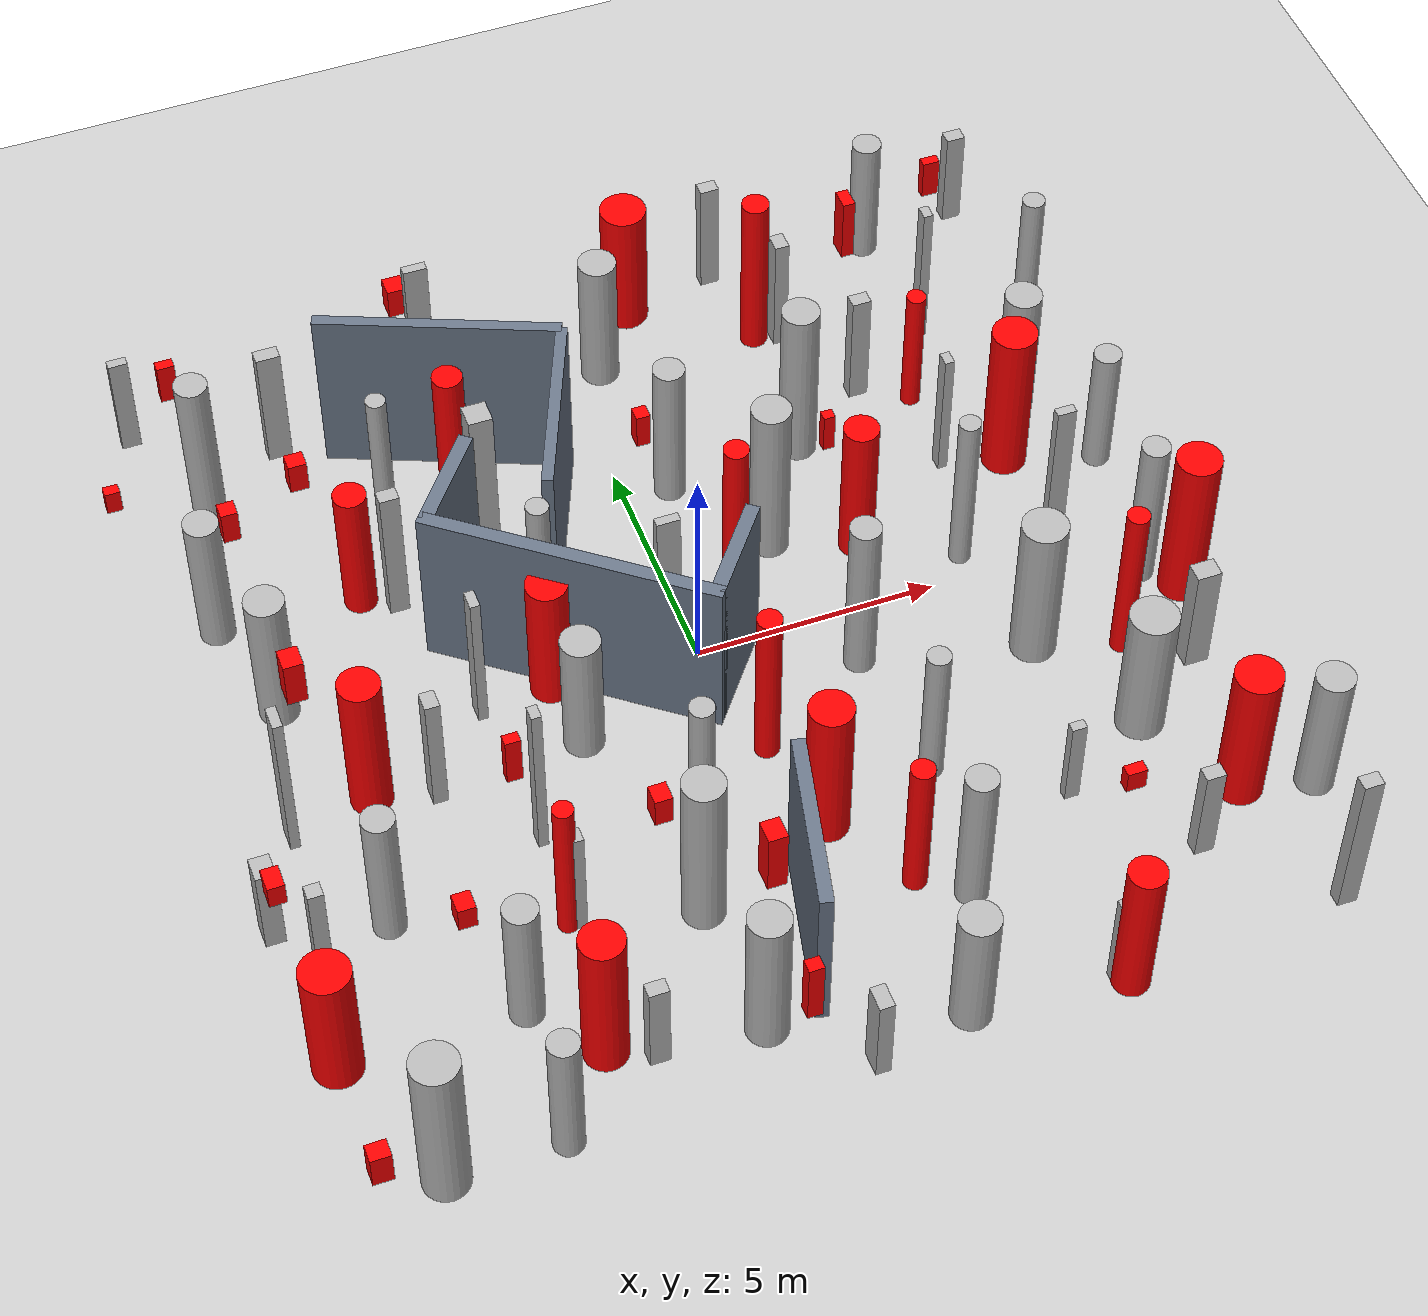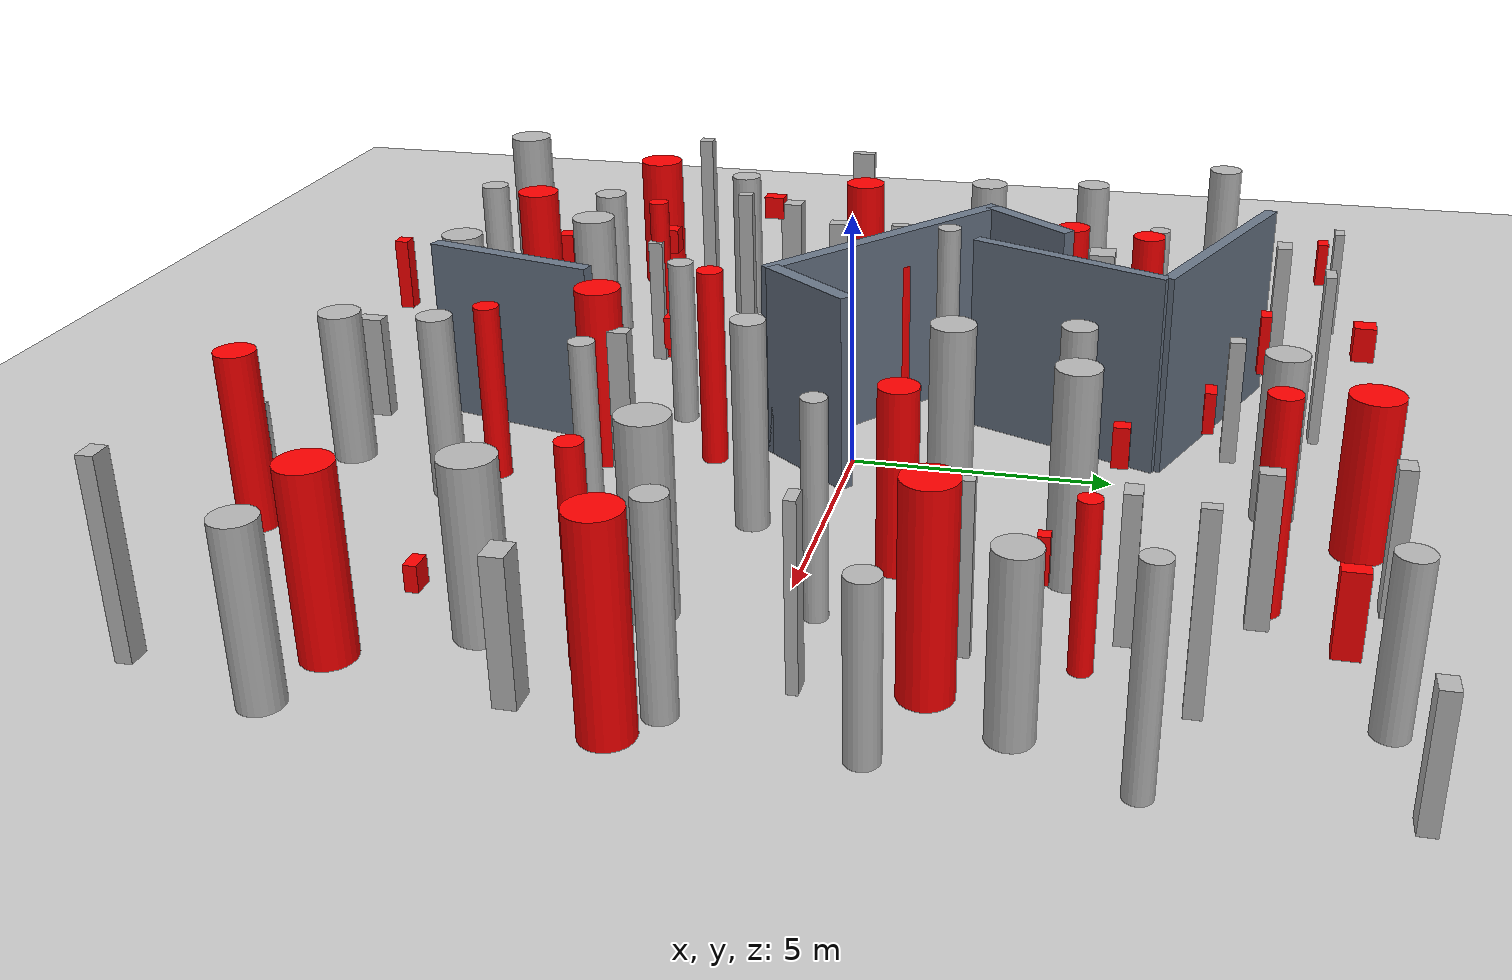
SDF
<sdf version='1.7'>
            <world name='default'>
                <light name='sun' type='directional'>
                <cast_shadows>1</cast_shadows>
                <pose>0 0 10 0 -0 0</pose>
                <diffuse>0.8 0.8 0.8 1</diffuse>
                <specular>0.2 0.2 0.2 1</specular>
                <attenuation>
                    <range>1000</range>
                    <constant>0.9</constant>
                    <linear>0.01</linear>
                    <quadratic>0.001</quadratic>
                </attenuation>
                <direction>-0.5 0.1 -0.9</direction>
                <spot>
                    <inner_angle>0</inner_angle>
                    <outer_angle>0</outer_angle>
                    <falloff>0</falloff>
                </spot>
                </light>
                <model name='ground_plane'>
                <static>1</static>
                <link name='link'>
                    <collision name='collision'>
                    <geometry>
                        <plane>
                        <normal>0 0 1</normal>
                        <size>100 100</size>
                        </plane>
                    </geometry>
                    <surface>
                        <contact>
                        <collide_bitmask>65535</collide_bitmask>
                        <ode/>
                        </contact>
                        <friction>
                        <ode>
                            <mu>100</mu>
                            <mu2>50</mu2>
                        </ode>
                        <torsional>
                            <ode/>
                        </torsional>
                        </friction>
                        <bounce/>
                    </surface>
                    <max_contacts>10</max_contacts>
                    </collision>
                    <visual name='visual'>
                    <cast_shadows>0</cast_shadows>
                    <geometry>
                        <plane>
                        <normal>0 0 1</normal>
                        <size>100 100</size>
                        </plane>
                    </geometry>
                    <material>
                        <script>
                        <uri>file://media/materials/scripts/gazebo.material</uri>
                        <name>Gazebo/Grey</name>
                        </script>
                    </material>
                    </visual>
                    <self_collide>0</self_collide>
                    <enable_wind>0</enable_wind>
                    <kinematic>0</kinematic>
                </link>
                </model>
                <gravity>0 0 -9.8</gravity>
                <magnetic_field>6e-06 2.3e-05 -4.2e-05</magnetic_field>
                <atmosphere type='adiabatic'/>
                <physics type='ode'>
                <max_step_size>0.001</max_step_size>
                <real_time_factor>1</real_time_factor>
                <real_time_update_rate>1000</real_time_update_rate>
                </physics>
                <scene>
                <ambient>0.4 0.4 0.4 1</ambient>
                <background>0.7 0.7 0.7 1</background>
                <shadows>1</shadows>
                </scene>
                <wind/>
                <spherical_coordinates>
                <surface_model>EARTH_WGS84</surface_model>
                <latitude_deg>0</latitude_deg>
                <longitude_deg>0</longitude_deg>
                <elevation>0</elevation>
                <heading_deg>0</heading_deg>
                </spherical_coordinates>

                            <model name='cylinder_0_0.7_0.7_3.5'>
                            <static>true</static>
                            <pose>0.9762700785464951 4.30378732744839 1.7724415914984484 0 0 0</pose> <!-- X, Y, Z, Roll, Pitch, Yaw -->
                            <link name='link'>
                                <collision name='collision'>
                                <geometry>
                                    <cylinder>
                                        <radius>0.3270964398016714</radius>
                                        <length>3.5448831829968968</length>
                                    </cylinder>
                                </geometry>
                                </collision>
                                <visual name='visual'>
                                <geometry>
                                    <cylinder>
                                        <radius>0.3270964398016714</radius>
                                        <length>3.5448831829968968</length>
                                    </cylinder>
                                </geometry>
                                </visual>
                            </link>
                            </model>

                            <model name='cylinder_1_0.6_0.6_4.0'>
                            <static>true</static>
                            <pose>2.9178822613331223 -1.2482557747461498 1.9818313802505148 0 0 0</pose> <!-- X, Y, Z, Roll, Pitch, Yaw -->
                            <link name='link'>
                                <collision name='collision'>
                                <geometry>
                                    <cylinder>
                                        <radius>0.3150324556477333</radius>
                                        <length>3.9636627605010295</length>
                                    </cylinder>
                                </geometry>
                                </collision>
                                <visual name='visual'>
                                <geometry>
                                    <cylinder>
                                        <radius>0.3150324556477333</radius>
                                        <length>3.9636627605010295</length>
                                    </cylinder>
                                </geometry>
                                </visual>
                            </link>
                            </model>

                            <model name='cylinder_2_0.4_0.4_3.9'>
                            <static>true</static>
                            <pose>5.834500761653292 0.5778983950580896 1.9627983191463305 0 0 0</pose> <!-- X, Y, Z, Roll, Pitch, Yaw -->
                            <link name='link'>
                                <collision name='collision'>
                                <geometry>
                                    <cylinder>
                                        <radius>0.2213108174593661</radius>
                                        <length>3.925596638292661</length>
                                    </cylinder>
                                </geometry>
                                </collision>
                                <visual name='visual'>
                                <geometry>
                                    <cylinder>
                                        <radius>0.2213108174593661</radius>
                                        <length>3.925596638292661</length>
                                    </cylinder>
                                </geometry>
                                </visual>
                            </link>
                            </model>

                            <model name='cylinder_3_0.9_0.9_3.8'>
                            <static>true</static>
                            <pose>-8.257414005969185 -9.595632051193485 1.8890783754749252 0 0 0</pose> <!-- X, Y, Z, Roll, Pitch, Yaw -->
                            <link name='link'>
                                <collision name='collision'>
                                <geometry>
                                    <cylinder>
                                        <radius>0.46100364447404574</radius>
                                        <length>3.7781567509498504</length>
                                    </cylinder>
                                </geometry>
                                </collision>
                                <visual name='visual'>
                                <geometry>
                                    <cylinder>
                                        <radius>0.46100364447404574</radius>
                                        <length>3.7781567509498504</length>
                                    </cylinder>
                                </geometry>
                                </visual>
                            </link>
                            </model>

                            <model name='cylinder_4_0.5_0.5_3.8'>
                            <static>true</static>
                            <pose>9.57236684465528 5.983171284334472 1.8902645881432276 0 0 0</pose> <!-- X, Y, Z, Roll, Pitch, Yaw -->
                            <link name='link'>
                                <collision name='collision'>
                                <geometry>
                                    <cylinder>
                                        <radius>0.23548232776067998</radius>
                                        <length>3.7805291762864552</length>
                                    </cylinder>
                                </geometry>
                                </collision>
                                <visual name='visual'>
                                <geometry>
                                    <cylinder>
                                        <radius>0.23548232776067998</radius>
                                        <length>3.7805291762864552</length>
                                    </cylinder>
                                </geometry>
                                </visual>
                            </link>
                            </model>

                            <model name='cylinder_5_0.6_0.6_3.5'>
                            <static>true</static>
                            <pose>2.7984204265504764 -7.132934251819072 1.760924160875036 0 0 0</pose> <!-- X, Y, Z, Roll, Pitch, Yaw -->
                            <link name='link'>
                                <collision name='collision'>
                                <geometry>
                                    <cylinder>
                                        <radius>0.3243985819971571</radius>
                                        <length>3.521848321750072</length>
                                    </cylinder>
                                </geometry>
                                </collision>
                                <visual name='visual'>
                                <geometry>
                                    <cylinder>
                                        <radius>0.3243985819971571</radius>
                                        <length>3.521848321750072</length>
                                    </cylinder>
                                </geometry>
                                </visual>
                            </link>
                            </model>

                            <model name='cylinder_6_0.4_0.4_3.6'>
                            <static>true</static>
                            <pose>-4.70888775790746 5.484673788684333 1.7842169744343241 0 0 0</pose> <!-- X, Y, Z, Roll, Pitch, Yaw -->
                            <link name='link'>
                                <collision name='collision'>
                                <geometry>
                                    <cylinder>
                                        <radius>0.20563694013090655</radius>
                                        <length>3.5684339488686483</length>
                                    </cylinder>
                                </geometry>
                                </collision>
                                <visual name='visual'>
                                <geometry>
                                    <cylinder>
                                        <radius>0.20563694013090655</radius>
                                        <length>3.5684339488686483</length>
                                    </cylinder>
                                </geometry>
                                </visual>
                            </link>
                            </model>

                            <model name='cylinder_7_0.8_0.8_3.9'>
                            <static>true</static>
                            <pose>2.352709941517541 2.241914454448428 1.9718740392573122 0 0 0</pose> <!-- X, Y, Z, Roll, Pitch, Yaw -->
                            <link name='link'>
                                <collision name='collision'>
                                <geometry>
                                    <cylinder>
                                        <radius>0.404546089731045</radius>
                                        <length>3.9437480785146244</length>
                                    </cylinder>
                                </geometry>
                                </collision>
                                <visual name='visual'>
                                <geometry>
                                    <cylinder>
                                        <radius>0.404546089731045</radius>
                                        <length>3.9437480785146244</length>
                                    </cylinder>
                                </geometry>
                                </visual>
                            </link>
                            </model>

                            <model name='cylinder_8_0.8_0.8_3.1'>
                            <static>true</static>
                            <pose>-2.80984198852428 -1.259360924013171 1.530112735814635 0 0 0</pose> <!-- X, Y, Z, Roll, Pitch, Yaw -->
                            <link name='link'>
                                <collision name='collision'>
                                <geometry>
                                    <cylinder>
                                        <radius>0.4000300146337003</radius>
                                        <length>3.06022547162927</length>
                                    </cylinder>
                                </geometry>
                                </collision>
                                <visual name='visual'>
                                <geometry>
                                    <cylinder>
                                        <radius>0.4000300146337003</radius>
                                        <length>3.06022547162927</length>
                                    </cylinder>
                                </geometry>
                                </visual>
                            </link>
                            </model>

                            <model name='cylinder_9_0.5_0.5_4.0'>
                            <static>true</static>
                            <pose>-2.725784581147548 1.4039354083575928 1.994186919029613 0 0 0</pose> <!-- X, Y, Z, Roll, Pitch, Yaw -->
                            <link name='link'>
                                <collision name='collision'>
                                <geometry>
                                    <cylinder>
                                        <radius>0.23061344322440844</radius>
                                        <length>3.988373838059226</length>
                                    </cylinder>
                                </geometry>
                                </collision>
                                <visual name='visual'>
                                <geometry>
                                    <cylinder>
                                        <radius>0.23061344322440844</radius>
                                        <length>3.988373838059226</length>
                                    </cylinder>
                                </geometry>
                                </visual>
                            </link>
                            </model>

                            <model name='cylinder_10_0.7_0.7_3.3'>
                            <static>true</static>
                            <pose>-5.822464878103306 -6.773809642300074 1.626645801269891 0 0 0</pose> <!-- X, Y, Z, Roll, Pitch, Yaw -->
                            <link name='link'>
                                <collision name='collision'>
                                <geometry>
                                    <cylinder>
                                        <radius>0.3398932318568919</radius>
                                        <length>3.253291602539782</length>
                                    </cylinder>
                                </geometry>
                                </collision>
                                <visual name='visual'>
                                <geometry>
                                    <cylinder>
                                        <radius>0.3398932318568919</radius>
                                        <length>3.253291602539782</length>
                                    </cylinder>
                                </geometry>
                                </visual>
                            </link>
                            </model>

                            <model name='cylinder_11_0.7_0.7_4.0'>
                            <static>true</static>
                            <pose>-8.057974484138775 6.758898149976078 1.988229732506698 0 0 0</pose> <!-- X, Y, Z, Roll, Pitch, Yaw -->
                            <link name='link'>
                                <collision name='collision'>
                                <geometry>
                                    <cylinder>
                                        <radius>0.3405953604943105</radius>
                                        <length>3.976459465013396</length>
                                    </cylinder>
                                </geometry>
                                </collision>
                                <visual name='visual'>
                                <geometry>
                                    <cylinder>
                                        <radius>0.3405953604943105</radius>
                                        <length>3.976459465013396</length>
                                    </cylinder>
                                </geometry>
                                </visual>
                            </link>
                            </model>

                            <model name='cylinder_12_0.6_0.6_3.0'>
                            <static>true</static>
                            <pose>9.535221763806742 2.0969103949009193 1.5195938961271604 0 0 0</pose> <!-- X, Y, Z, Roll, Pitch, Yaw -->
                            <link name='link'>
                                <collision name='collision'>
                                <geometry>
                                    <cylinder>
                                        <radius>0.2848420887729229</radius>
                                        <length>3.039187792254321</length>
                                    </cylinder>
                                </geometry>
                                </collision>
                                <visual name='visual'>
                                <geometry>
                                    <cylinder>
                                        <radius>0.2848420887729229</radius>
                                        <length>3.039187792254321</length>
                                    </cylinder>
                                </geometry>
                                </visual>
                            </link>
                            </model>

                            <model name='cylinder_13_0.6_0.6_3.3'>
                            <static>true</static>
                            <pose>-7.596068775736622 -4.077196049557101 1.658991589696988 0 0 0</pose> <!-- X, Y, Z, Roll, Pitch, Yaw -->
                            <link name='link'>
                                <collision name='collision'>
                                <geometry>
                                    <cylinder>
                                        <radius>0.324278898354401</radius>
                                        <length>3.317983179393976</length>
                                    </cylinder>
                                </geometry>
                                </collision>
                                <visual name='visual'>
                                <geometry>
                                    <cylinder>
                                        <radius>0.324278898354401</radius>
                                        <length>3.317983179393976</length>
                                    </cylinder>
                                </geometry>
                                </visual>
                            </link>
                            </model>

                            <model name='cylinder_14_0.7_0.7_3.3'>
                            <static>true</static>
                            <pose>-8.717050073024312 3.849442387400397 1.6326947454697227 0 0 0</pose> <!-- X, Y, Z, Roll, Pitch, Yaw -->
                            <link name='link'>
                                <collision name='collision'>
                                <geometry>
                                    <cylinder>
                                        <radius>0.3569744160400099</radius>
                                        <length>3.2653894909394454</length>
                                    </cylinder>
                                </geometry>
                                </collision>
                                <visual name='visual'>
                                <geometry>
                                    <cylinder>
                                        <radius>0.3569744160400099</radius>
                                        <length>3.2653894909394454</length>
                                    </cylinder>
                                </geometry>
                                </visual>
                            </link>
                            </model>

                            <model name='cylinder_15_0.8_0.8_3.3'>
                            <static>true</static>
                            <pose>-8.121189784831166 1.5189299111235854 1.6592844762256618 0 0 0</pose> <!-- X, Y, Z, Roll, Pitch, Yaw -->
                            <link name='link'>
                                <collision name='collision'>
                                <geometry>
                                    <cylinder>
                                        <radius>0.4002231139891045</radius>
                                        <length>3.3185689524513236</length>
                                    </cylinder>
                                </geometry>
                                </collision>
                                <visual name='visual'>
                                <geometry>
                                    <cylinder>
                                        <radius>0.4002231139891045</radius>
                                        <length>3.3185689524513236</length>
                                    </cylinder>
                                </geometry>
                                </visual>
                            </link>
                            </model>

                            <model name='cylinder_16_0.8_0.8_3.0'>
                            <static>true</static>
                            <pose>1.730258696201663 -9.597849076250128 1.5023477380962735 0 0 0</pose> <!-- X, Y, Z, Roll, Pitch, Yaw -->
                            <link name='link'>
                                <collision name='collision'>
                                <geometry>
                                    <cylinder>
                                        <radius>0.403344961038869</radius>
                                        <length>3.004695476192547</length>
                                    </cylinder>
                                </geometry>
                                </collision>
                                <visual name='visual'>
                                <geometry>
                                    <cylinder>
                                        <radius>0.403344961038869</radius>
                                        <length>3.004695476192547</length>
                                    </cylinder>
                                </geometry>
                                </visual>
                            </link>
                            </model>

                            <model name='cylinder_17_0.6_0.6_3.7'>
                            <static>true</static>
                            <pose>9.0549802303397 -1.0574924276474529 1.849739637658752 0 0 0</pose> <!-- X, Y, Z, Roll, Pitch, Yaw -->
                            <link name='link'>
                                <collision name='collision'>
                                <geometry>
                                    <cylinder>
                                        <radius>0.2892310852565401</radius>
                                        <length>3.699479275317504</length>
                                    </cylinder>
                                </geometry>
                                </collision>
                                <visual name='visual'>
                                <geometry>
                                    <cylinder>
                                        <radius>0.2892310852565401</radius>
                                        <length>3.699479275317504</length>
                                    </cylinder>
                                </geometry>
                                </visual>
                            </link>
                            </model>

                            <model name='cylinder_18_0.9_0.9_3.6'>
                            <static>true</static>
                            <pose>6.275956394049544 -2.069885183060307 1.7906364363179295 0 0 0</pose> <!-- X, Y, Z, Roll, Pitch, Yaw -->
                            <link name='link'>
                                <collision name='collision'>
                                <geometry>
                                    <cylinder>
                                        <radius>0.4645206085564558</radius>
                                        <length>3.581272872635859</length>
                                    </cylinder>
                                </geometry>
                                </collision>
                                <visual name='visual'>
                                <geometry>
                                    <cylinder>
                                        <radius>0.4645206085564558</radius>
                                        <length>3.581272872635859</length>
                                    </cylinder>
                                </geometry>
                                </visual>
                            </link>
                            </model>

                            <model name='cylinder_19_0.8_0.8_4.0'>
                            <static>true</static>
                            <pose>3.8506318015553176 4.50508559639281 1.9780418173616119 0 0 0</pose> <!-- X, Y, Z, Roll, Pitch, Yaw -->
                            <link name='link'>
                                <collision name='collision'>
                                <geometry>
                                    <cylinder>
                                        <radius>0.39319705976889124</radius>
                                        <length>3.9560836347232238</length>
                                    </cylinder>
                                </geometry>
                                </collision>
                                <visual name='visual'>
                                <geometry>
                                    <cylinder>
                                        <radius>0.39319705976889124</radius>
                                        <length>3.9560836347232238</length>
                                    </cylinder>
                                </geometry>
                                </visual>
                            </link>
                            </model>

                            <model name='cylinder_20_0.5_0.5_3.4'>
                            <static>true</static>
                            <pose>3.2034707498537007 -4.198447855791119 1.714384350472883 0 0 0</pose> <!-- X, Y, Z, Roll, Pitch, Yaw -->
                            <link name='link'>
                                <collision name='collision'>
                                <geometry>
                                    <cylinder>
                                        <radius>0.24064221926673507</radius>
                                        <length>3.428768700945766</length>
                                    </cylinder>
                                </geometry>
                                </collision>
                                <visual name='visual'>
                                <geometry>
                                    <cylinder>
                                        <radius>0.24064221926673507</radius>
                                        <length>3.428768700945766</length>
                                    </cylinder>
                                </geometry>
                                </visual>
                            </link>
                            </model>

                            <model name='cylinder_21_0.8_0.8_3.2'>
                            <static>true</static>
                            <pose>9.976940131357331 -7.011033906840125 1.5812464673381874 0 0 0</pose> <!-- X, Y, Z, Roll, Pitch, Yaw -->
                            <link name='link'>
                                <collision name='collision'>
                                <geometry>
                                    <cylinder>
                                        <radius>0.38466786928515323</radius>
                                        <length>3.162492934676375</length>
                                    </cylinder>
                                </geometry>
                                </collision>
                                <visual name='visual'>
                                <geometry>
                                    <cylinder>
                                        <radius>0.38466786928515323</radius>
                                        <length>3.162492934676375</length>
                                    </cylinder>
                                </geometry>
                                </visual>
                            </link>
                            </model>

                            <model name='cylinder_22_0.8_0.8_3.5'>
                            <static>true</static>
                            <pose>-1.8563340554800067 -8.61666009089724 1.7267713413390344 0 0 0</pose> <!-- X, Y, Z, Roll, Pitch, Yaw -->
                            <link name='link'>
                                <collision name='collision'>
                                <geometry>
                                    <cylinder>
                                        <radius>0.4166166798411044</radius>
                                        <length>3.453542682678069</length>
                                    </cylinder>
                                </geometry>
                                </collision>
                                <visual name='visual'>
                                <geometry>
                                    <cylinder>
                                        <radius>0.4166166798411044</radius>
                                        <length>3.453542682678069</length>
                                    </cylinder>
                                </geometry>
                                </visual>
                            </link>
                            </model>

                            <model name='cylinder_23_0.6_0.6_3.0'>
                            <static>true</static>
                            <pose>7.327646518572584 9.510430100057716 1.505857042092501 0 0 0</pose> <!-- X, Y, Z, Roll, Pitch, Yaw -->
                            <link name='link'>
                                <collision name='collision'>
                                <geometry>
                                    <cylinder>
                                        <radius>0.30799341934350916</radius>
                                        <length>3.011714084185002</length>
                                    </cylinder>
                                </geometry>
                                </collision>
                                <visual name='visual'>
                                <geometry>
                                    <cylinder>
                                        <radius>0.30799341934350916</radius>
                                        <length>3.011714084185002</length>
                                    </cylinder>
                                </geometry>
                                </visual>
                            </link>
                            </model>

                            <model name='cylinder_24_0.6_0.6_3.2'>
                            <static>true</static>
                            <pose>-6.000069502071998 -9.62956411078772 1.61196234403019 0 0 0</pose> <!-- X, Y, Z, Roll, Pitch, Yaw -->
                            <link name='link'>
                                <collision name='collision'>
                                <geometry>
                                    <cylinder>
                                        <radius>0.30360550420907084</radius>
                                        <length>3.22392468806038</length>
                                    </cylinder>
                                </geometry>
                                </collision>
                                <visual name='visual'>
                                <geometry>
                                    <cylinder>
                                        <radius>0.30360550420907084</radius>
                                        <length>3.22392468806038</length>
                                    </cylinder>
                                </geometry>
                                </visual>
                            </link>
                            </model>

                            <model name='cylinder_25_0.8_0.8_3.2'>
                            <static>true</static>
                            <pose>8.561625869311818 4.0882880384706555 1.5823470782489564 0 0 0</pose> <!-- X, Y, Z, Roll, Pitch, Yaw -->
                            <link name='link'>
                                <collision name='collision'>
                                <geometry>
                                    <cylinder>
                                        <radius>0.3864435204499291</radius>
                                        <length>3.1646941564979127</length>
                                    </cylinder>
                                </geometry>
                                </collision>
                                <visual name='visual'>
                                <geometry>
                                    <cylinder>
                                        <radius>0.3864435204499291</radius>
                                        <length>3.1646941564979127</length>
                                    </cylinder>
                                </geometry>
                                </visual>
                            </link>
                            </model>

                            <model name='cylinder_26_0.8_0.8_3.9'>
                            <static>true</static>
                            <pose>-2.0355787556781624 -5.803125020497557 1.9721861949919668 0 0 0</pose> <!-- X, Y, Z, Roll, Pitch, Yaw -->
                            <link name='link'>
                                <collision name='collision'>
                                <geometry>
                                    <cylinder>
                                        <radius>0.42186523851478624</radius>
                                        <length>3.9443723899839336</length>
                                    </cylinder>
                                </geometry>
                                </collision>
                                <visual name='visual'>
                                <geometry>
                                    <cylinder>
                                        <radius>0.42186523851478624</radius>
                                        <length>3.9443723899839336</length>
                                    </cylinder>
                                </geometry>
                                </visual>
                            </link>
                            </model>

                            <model name='cylinder_27_0.5_0.5_3.4'>
                            <static>true</static>
                            <pose>-1.3116674888375845 -3.7640823601179485 1.6888759196462404 0 0 0</pose> <!-- X, Y, Z, Roll, Pitch, Yaw -->
                            <link name='link'>
                                <collision name='collision'>
                                <geometry>
                                    <cylinder>
                                        <radius>0.25388110326789043</radius>
                                        <length>3.377751839292481</length>
                                    </cylinder>
                                </geometry>
                                </collision>
                                <visual name='visual'>
                                <geometry>
                                    <cylinder>
                                        <radius>0.25388110326789043</radius>
                                        <length>3.377751839292481</length>
                                    </cylinder>
                                </geometry>
                                </visual>
                            </link>
                            </model>

                            <model name='cylinder_28_0.8_0.8_3.2'>
                            <static>true</static>
                            <pose>0.731584222174444 7.933425860806842 1.608448492199237 0 0 0</pose> <!-- X, Y, Z, Roll, Pitch, Yaw -->
                            <link name='link'>
                                <collision name='collision'>
                                <geometry>
                                    <cylinder>
                                        <radius>0.3989234609300302</radius>
                                        <length>3.216896984398474</length>
                                    </cylinder>
                                </geometry>
                                </collision>
                                <visual name='visual'>
                                <geometry>
                                    <cylinder>
                                        <radius>0.3989234609300302</radius>
                                        <length>3.216896984398474</length>
                                    </cylinder>
                                </geometry>
                                </visual>
                            </link>
                            </model>

                            <model name='cylinder_29_1.0_1.0_3.2'>
                            <static>true</static>
                            <pose>7.453013108947905 -4.529159303687285 1.592817972152976 0 0 0</pose> <!-- X, Y, Z, Roll, Pitch, Yaw -->
                            <link name='link'>
                                <collision name='collision'>
                                <geometry>
                                    <cylinder>
                                        <radius>0.48583749709158336</radius>
                                        <length>3.185635944305952</length>
                                    </cylinder>
                                </geometry>
                                </collision>
                                <visual name='visual'>
                                <geometry>
                                    <cylinder>
                                        <radius>0.48583749709158336</radius>
                                        <length>3.185635944305952</length>
                                    </cylinder>
                                </geometry>
                                </visual>
                            </link>
                            </model>

                            <model name='box_0_0.3_0.4_2.9'>
                            <static>true</static>
                            <pose>-5.850598491177812 -1.5062906249698749 1.4635754243648107 0 0 0</pose> <!-- X, Y, Z, Roll, Pitch, Yaw -->
                            <link name='link'>
                                <collision name='collision'>
                                <geometry>
                                    <box>
                                        <size>0.3 0.4 2.9</size> <!-- Width, Depth, Height -->
                                    </box>
                                </geometry>
                                </collision>
                                <visual name='visual'>
                                <geometry>
                                    <box>
                                        <size>0.3 0.4 2.9</size> <!-- Width, Depth, Height -->
                                    </box>
                                </geometry>
                                </visual>
                            </link>
                            </model>

                            <model name='box_1_0.4_0.3_2.3'>
                            <static>true</static>
                            <pose>7.277112118464628 -7.649362880759338 1.1320681063451534 0 0 0</pose> <!-- X, Y, Z, Roll, Pitch, Yaw -->
                            <link name='link'>
                                <collision name='collision'>
                                <geometry>
                                    <box>
                                        <size>0.4 0.3 2.3</size> <!-- Width, Depth, Height -->
                                    </box>
                                </geometry>
                                </collision>
                                <visual name='visual'>
                                <geometry>
                                    <box>
                                        <size>0.4 0.3 2.3</size> <!-- Width, Depth, Height -->
                                    </box>
                                </geometry>
                                </visual>
                            </link>
                            </model>

                            <model name='box_2_0.5_0.2_3.5'>
                            <static>true</static>
                            <pose>-2.8877452430008876 8.808638905056261 1.7486636198505474 0 0 0</pose> <!-- X, Y, Z, Roll, Pitch, Yaw -->
                            <link name='link'>
                                <collision name='collision'>
                                <geometry>
                                    <box>
                                        <size>0.5 0.2 3.5</size> <!-- Width, Depth, Height -->
                                    </box>
                                </geometry>
                                </collision>
                                <visual name='visual'>
                                <geometry>
                                    <box>
                                        <size>0.5 0.2 3.5</size> <!-- Width, Depth, Height -->
                                    </box>
                                </geometry>
                                </visual>
                            </link>
                            </model>

                            <model name='box_3_0.2_0.2_2.3'>
                            <static>true</static>
                            <pose>4.511887284211575 -9.771450827499379 1.1469466454003752 0 0 0</pose> <!-- X, Y, Z, Roll, Pitch, Yaw -->
                            <link name='link'>
                                <collision name='collision'>
                                <geometry>
                                    <box>
                                        <size>0.2 0.2 2.3</size> <!-- Width, Depth, Height -->
                                    </box>
                                </geometry>
                                </collision>
                                <visual name='visual'>
                                <geometry>
                                    <box>
                                        <size>0.2 0.2 2.3</size> <!-- Width, Depth, Height -->
                                    </box>
                                </geometry>
                                </visual>
                            </link>
                            </model>

                            <model name='box_4_0.4_0.3_2.7'>
                            <static>true</static>
                            <pose>5.5739079188220675 5.5481512369750625 1.3738131379325615 0 0 0</pose> <!-- X, Y, Z, Roll, Pitch, Yaw -->
                            <link name='link'>
                                <collision name='collision'>
                                <geometry>
                                    <box>
                                        <size>0.4 0.3 2.7</size> <!-- Width, Depth, Height -->
                                    </box>
                                </geometry>
                                </collision>
                                <visual name='visual'>
                                <geometry>
                                    <box>
                                        <size>0.4 0.3 2.7</size> <!-- Width, Depth, Height -->
                                    </box>
                                </geometry>
                                </visual>
                            </link>
                            </model>

                            <model name='box_5_0.5_0.3_2.9'>
                            <static>true</static>
                            <pose>-6.257382164983105 8.07967909856474 1.4569114216457657 0 0 0</pose> <!-- X, Y, Z, Roll, Pitch, Yaw -->
                            <link name='link'>
                                <collision name='collision'>
                                <geometry>
                                    <box>
                                        <size>0.5 0.3 2.9</size> <!-- Width, Depth, Height -->
                                    </box>
                                </geometry>
                                </collision>
                                <visual name='visual'>
                                <geometry>
                                    <box>
                                        <size>0.5 0.3 2.9</size> <!-- Width, Depth, Height -->
                                    </box>
                                </geometry>
                                </visual>
                            </link>
                            </model>

                            <model name='box_6_0.2_0.5_3.7'>
                            <static>true</static>
                            <pose>-8.745740959533086 -1.519354962203161 1.849038308428511 0 0 0</pose> <!-- X, Y, Z, Roll, Pitch, Yaw -->
                            <link name='link'>
                                <collision name='collision'>
                                <geometry>
                                    <box>
                                        <size>0.2 0.5 3.7</size> <!-- Width, Depth, Height -->
                                    </box>
                                </geometry>
                                </collision>
                                <visual name='visual'>
                                <geometry>
                                    <box>
                                        <size>0.2 0.5 3.7</size> <!-- Width, Depth, Height -->
                                    </box>
                                </geometry>
                                </visual>
                            </link>
                            </model>

                            <model name='box_7_0.4_0.3_2.3'>
                            <static>true</static>
                            <pose>9.485124256361006 9.806900031217879 1.1629544260466054 0 0 0</pose> <!-- X, Y, Z, Roll, Pitch, Yaw -->
                            <link name='link'>
                                <collision name='collision'>
                                <geometry>
                                    <box>
                                        <size>0.4 0.3 2.3</size> <!-- Width, Depth, Height -->
                                    </box>
                                </geometry>
                                </collision>
                                <visual name='visual'>
                                <geometry>
                                    <box>
                                        <size>0.4 0.3 2.3</size> <!-- Width, Depth, Height -->
                                    </box>
                                </geometry>
                                </visual>
                            </link>
                            </model>

                            <model name='box_8_0.4_0.3_3.3'>
                            <static>true</static>
                            <pose>-5.17162759846852 3.250091430653519 1.6658591175591877 0 0 0</pose> <!-- X, Y, Z, Roll, Pitch, Yaw -->
                            <link name='link'>
                                <collision name='collision'>
                                <geometry>
                                    <box>
                                        <size>0.4 0.3 3.3</size> <!-- Width, Depth, Height -->
                                    </box>
                                </geometry>
                                </collision>
                                <visual name='visual'>
                                <geometry>
                                    <box>
                                        <size>0.4 0.3 3.3</size> <!-- Width, Depth, Height -->
                                    </box>
                                </geometry>
                                </visual>
                            </link>
                            </model>

                            <model name='box_9_0.3_0.4_2.8'>
                            <static>true</static>
                            <pose>1.0937561732283796 -4.258969601607405 1.4148568693335641 0 0 0</pose> <!-- X, Y, Z, Roll, Pitch, Yaw -->
                            <link name='link'>
                                <collision name='collision'>
                                <geometry>
                                    <box>
                                        <size>0.3 0.4 2.8</size> <!-- Width, Depth, Height -->
                                    </box>
                                </geometry>
                                </collision>
                                <visual name='visual'>
                                <geometry>
                                    <box>
                                        <size>0.3 0.4 2.8</size> <!-- Width, Depth, Height -->
                                    </box>
                                </geometry>
                                </visual>
                            </link>
                            </model>

                            <model name='box_10_0.3_0.4_2.8'>
                            <static>true</static>
                            <pose>4.614181982549523 7.634404246676794 1.3790568960774285 0 0 0</pose> <!-- X, Y, Z, Roll, Pitch, Yaw -->
                            <link name='link'>
                                <collision name='collision'>
                                <geometry>
                                    <box>
                                        <size>0.3 0.4 2.8</size> <!-- Width, Depth, Height -->
                                    </box>
                                </geometry>
                                </collision>
                                <visual name='visual'>
                                <geometry>
                                    <box>
                                        <size>0.3 0.4 2.8</size> <!-- Width, Depth, Height -->
                                    </box>
                                </geometry>
                                </visual>
                            </link>
                            </model>

                            <model name='box_11_0.4_0.3_3.6'>
                            <static>true</static>
                            <pose>9.255406396804847 -9.662566532599206 1.8136786497018633 0 0 0</pose> <!-- X, Y, Z, Roll, Pitch, Yaw -->
                            <link name='link'>
                                <collision name='collision'>
                                <geometry>
                                    <box>
                                        <size>0.4 0.3 3.6</size> <!-- Width, Depth, Height -->
                                    </box>
                                </geometry>
                                </collision>
                                <visual name='visual'>
                                <geometry>
                                    <box>
                                        <size>0.4 0.3 3.6</size> <!-- Width, Depth, Height -->
                                    </box>
                                </geometry>
                                </visual>
                            </link>
                            </model>

                            <model name='box_12_0.3_0.3_2.7'>
                            <static>true</static>
                            <pose>-4.320000464757978 -5.23173438151884 1.3679275805370414 0 0 0</pose> <!-- X, Y, Z, Roll, Pitch, Yaw -->
                            <link name='link'>
                                <collision name='collision'>
                                <geometry>
                                    <box>
                                        <size>0.3 0.3 2.7</size> <!-- Width, Depth, Height -->
                                    </box>
                                </geometry>
                                </collision>
                                <visual name='visual'>
                                <geometry>
                                    <box>
                                        <size>0.3 0.3 2.7</size> <!-- Width, Depth, Height -->
                                    </box>
                                </geometry>
                                </visual>
                            </link>
                            </model>

                            <model name='box_13_0.5_0.5_3.6'>
                            <static>true</static>
                            <pose>-2.962140076139148 4.428133359199049 1.8130538632474607 0 0 0</pose> <!-- X, Y, Z, Roll, Pitch, Yaw -->
                            <link name='link'>
                                <collision name='collision'>
                                <geometry>
                                    <box>
                                        <size>0.5 0.5 3.6</size> <!-- Width, Depth, Height -->
                                    </box>
                                </geometry>
                                </collision>
                                <visual name='visual'>
                                <geometry>
                                    <box>
                                        <size>0.5 0.5 3.6</size> <!-- Width, Depth, Height -->
                                    </box>
                                </geometry>
                                </visual>
                            </link>
                            </model>

                            <model name='box_14_0.5_0.2_2.3'>
                            <static>true</static>
                            <pose>-0.04446184349316429 1.6216385934412614 1.1690254061291614 0 0 0</pose> <!-- X, Y, Z, Roll, Pitch, Yaw -->
                            <link name='link'>
                                <collision name='collision'>
                                <geometry>
                                    <box>
                                        <size>0.5 0.2 2.3</size> <!-- Width, Depth, Height -->
                                    </box>
                                </geometry>
                                </collision>
                                <visual name='visual'>
                                <geometry>
                                    <box>
                                        <size>0.5 0.2 2.3</size> <!-- Width, Depth, Height -->
                                    </box>
                                </geometry>
                                </visual>
                            </link>
                            </model>

                            <model name='box_15_0.3_0.3_2.5'>
                            <static>true</static>
                            <pose>-1.5258729308905439 7.142498350091346 1.271252076761864 0 0 0</pose> <!-- X, Y, Z, Roll, Pitch, Yaw -->
                            <link name='link'>
                                <collision name='collision'>
                                <geometry>
                                    <box>
                                        <size>0.3 0.3 2.5</size> <!-- Width, Depth, Height -->
                                    </box>
                                </geometry>
                                </collision>
                                <visual name='visual'>
                                <geometry>
                                    <box>
                                        <size>0.3 0.3 2.5</size> <!-- Width, Depth, Height -->
                                    </box>
                                </geometry>
                                </visual>
                            </link>
                            </model>

                            <model name='box_16_0.2_0.3_3.1'>
                            <static>true</static>
                            <pose>6.448134767113807 3.068423222272738 1.5369230010823904 0 0 0</pose> <!-- X, Y, Z, Roll, Pitch, Yaw -->
                            <link name='link'>
                                <collision name='collision'>
                                <geometry>
                                    <box>
                                        <size>0.2 0.3 3.1</size> <!-- Width, Depth, Height -->
                                    </box>
                                </geometry>
                                </collision>
                                <visual name='visual'>
                                <geometry>
                                    <box>
                                        <size>0.2 0.3 3.1</size> <!-- Width, Depth, Height -->
                                    </box>
                                </geometry>
                                </visual>
                            </link>
                            </model>

                            <model name='box_17_0.3_0.2_2.7'>
                            <static>true</static>
                            <pose>0.6983370985416792 -1.9151276412148244 1.3650998770600098 0 0 0</pose> <!-- X, Y, Z, Roll, Pitch, Yaw -->
                            <link name='link'>
                                <collision name='collision'>
                                <geometry>
                                    <box>
                                        <size>0.3 0.2 2.7</size> <!-- Width, Depth, Height -->
                                    </box>
                                </geometry>
                                </collision>
                                <visual name='visual'>
                                <geometry>
                                    <box>
                                        <size>0.3 0.2 2.7</size> <!-- Width, Depth, Height -->
                                    </box>
                                </geometry>
                                </visual>
                            </link>
                            </model>

                            <model name='box_18_0.4_0.3_2.7'>
                            <static>true</static>
                            <pose>3.815695523130591 9.746975141479364 1.3645446259967866 0 0 0</pose> <!-- X, Y, Z, Roll, Pitch, Yaw -->
                            <link name='link'>
                                <collision name='collision'>
                                <geometry>
                                    <box>
                                        <size>0.4 0.3 2.7</size> <!-- Width, Depth, Height -->
                                    </box>
                                </geometry>
                                </collision>
                                <visual name='visual'>
                                <geometry>
                                    <box>
                                        <size>0.4 0.3 2.7</size> <!-- Width, Depth, Height -->
                                    </box>
                                </geometry>
                                </visual>
                            </link>
                            </model>

                            <model name='box_19_0.4_0.2_2.4'>
                            <static>true</static>
                            <pose>-9.063872905756226 9.414628855412657 1.1785799680576563 0 0 0</pose> <!-- X, Y, Z, Roll, Pitch, Yaw -->
                            <link name='link'>
                                <collision name='collision'>
                                <geometry>
                                    <box>
                                        <size>0.4 0.2 2.4</size> <!-- Width, Depth, Height -->
                                    </box>
                                </geometry>
                                </collision>
                                <visual name='visual'>
                                <geometry>
                                    <box>
                                        <size>0.4 0.2 2.4</size> <!-- Width, Depth, Height -->
                                    </box>
                                </geometry>
                                </visual>
                            </link>
                            </model>

                            <model name='box_20_0.4_0.3_2.2'>
                            <static>true</static>
                            <pose>-3.9160261680118436 -8.492818618333192 1.107617705149582 0 0 0</pose> <!-- X, Y, Z, Roll, Pitch, Yaw -->
                            <link name='link'>
                                <collision name='collision'>
                                <geometry>
                                    <box>
                                        <size>0.4 0.3 2.2</size> <!-- Width, Depth, Height -->
                                    </box>
                                </geometry>
                                </collision>
                                <visual name='visual'>
                                <geometry>
                                    <box>
                                        <size>0.4 0.3 2.2</size> <!-- Width, Depth, Height -->
                                    </box>
                                </geometry>
                                </visual>
                            </link>
                            </model>

                            <model name='box_21_0.3_0.5_2.1'>
                            <static>true</static>
                            <pose>-0.24647352923584886 -9.989080702060086 1.0635537748361585 0 0 0</pose> <!-- X, Y, Z, Roll, Pitch, Yaw -->
                            <link name='link'>
                                <collision name='collision'>
                                <geometry>
                                    <box>
                                        <size>0.3 0.5 2.1</size> <!-- Width, Depth, Height -->
                                    </box>
                                </geometry>
                                </collision>
                                <visual name='visual'>
                                <geometry>
                                    <box>
                                        <size>0.3 0.5 2.1</size> <!-- Width, Depth, Height -->
                                    </box>
                                </geometry>
                                </visual>
                            </link>
                            </model>

                            <model name='box_22_0.2_0.3_3.9'>
                            <static>true</static>
                            <pose>-4.343262956478342 -3.207379116676017 1.96319729526038 0 0 0</pose> <!-- X, Y, Z, Roll, Pitch, Yaw -->
                            <link name='link'>
                                <collision name='collision'>
                                <geometry>
                                    <box>
                                        <size>0.2 0.3 3.9</size> <!-- Width, Depth, Height -->
                                    </box>
                                </geometry>
                                </collision>
                                <visual name='visual'>
                                <geometry>
                                    <box>
                                        <size>0.2 0.3 3.9</size> <!-- Width, Depth, Height -->
                                    </box>
                                </geometry>
                                </visual>
                            </link>
                            </model>

                            <model name='box_23_0.3_0.2_2.1'>
                            <static>true</static>
                            <pose>5.4622010501083835 -5.662594998179187 1.042924190608832 0 0 0</pose> <!-- X, Y, Z, Roll, Pitch, Yaw -->
                            <link name='link'>
                                <collision name='collision'>
                                <geometry>
                                    <box>
                                        <size>0.3 0.2 2.1</size> <!-- Width, Depth, Height -->
                                    </box>
                                </geometry>
                                </collision>
                                <visual name='visual'>
                                <geometry>
                                    <box>
                                        <size>0.3 0.2 2.1</size> <!-- Width, Depth, Height -->
                                    </box>
                                </geometry>
                                </visual>
                            </link>
                            </model>

                            <model name='box_24_0.2_0.3_3.5'>
                            <static>true</static>
                            <pose>7.476643566694364 6.679632877532635 1.7712254629659103 0 0 0</pose> <!-- X, Y, Z, Roll, Pitch, Yaw -->
                            <link name='link'>
                                <collision name='collision'>
                                <geometry>
                                    <box>
                                        <size>0.2 0.3 3.5</size> <!-- Width, Depth, Height -->
                                    </box>
                                </geometry>
                                </collision>
                                <visual name='visual'>
                                <geometry>
                                    <box>
                                        <size>0.2 0.3 3.5</size> <!-- Width, Depth, Height -->
                                    </box>
                                </geometry>
                                </visual>
                            </link>
                            </model>

                            <model name='box_25_0.5_0.4_2.6'>
                            <static>true</static>
                            <pose>9.122463191199198 -3.3911885479431225 1.2808594946322427 0 0 0</pose> <!-- X, Y, Z, Roll, Pitch, Yaw -->
                            <link name='link'>
                                <collision name='collision'>
                                <geometry>
                                    <box>
                                        <size>0.5 0.4 2.6</size> <!-- Width, Depth, Height -->
                                    </box>
                                </geometry>
                                </collision>
                                <visual name='visual'>
                                <geometry>
                                    <box>
                                        <size>0.5 0.4 2.6</size> <!-- Width, Depth, Height -->
                                    </box>
                                </geometry>
                                </visual>
                            </link>
                            </model>

                            <model name='box_26_0.2_0.4_3.4'>
                            <static>true</static>
                            <pose>-4.467005395816209 0.12685838647608305 1.706410577667011 0 0 0</pose> <!-- X, Y, Z, Roll, Pitch, Yaw -->
                            <link name='link'>
                                <collision name='collision'>
                                <geometry>
                                    <box>
                                        <size>0.2 0.4 3.4</size> <!-- Width, Depth, Height -->
                                    </box>
                                </geometry>
                                </collision>
                                <visual name='visual'>
                                <geometry>
                                    <box>
                                        <size>0.2 0.4 3.4</size> <!-- Width, Depth, Height -->
                                    </box>
                                </geometry>
                                </visual>
                            </link>
                            </model>

                            <model name='box_27_0.4_0.2_3.3'>
                            <static>true</static>
                            <pose>7.972753368165324 0.7434025589741489 1.6736532695846353 0 0 0</pose> <!-- X, Y, Z, Roll, Pitch, Yaw -->
                            <link name='link'>
                                <collision name='collision'>
                                <geometry>
                                    <box>
                                        <size>0.4 0.2 3.3</size> <!-- Width, Depth, Height -->
                                    </box>
                                </geometry>
                                </collision>
                                <visual name='visual'>
                                <geometry>
                                    <box>
                                        <size>0.4 0.2 3.3</size> <!-- Width, Depth, Height -->
                                    </box>
                                </geometry>
                                </visual>
                            </link>
                            </model>

                            <model name='box_28_0.3_0.3_3.7'>
                            <static>true</static>
                            <pose>-9.152719058171135 -5.44518013305427 1.8369903652886839 0 0 0</pose> <!-- X, Y, Z, Roll, Pitch, Yaw -->
                            <link name='link'>
                                <collision name='collision'>
                                <geometry>
                                    <box>
                                        <size>0.3 0.3 3.7</size> <!-- Width, Depth, Height -->
                                    </box>
                                </geometry>
                                </collision>
                                <visual name='visual'>
                                <geometry>
                                    <box>
                                        <size>0.3 0.3 3.7</size> <!-- Width, Depth, Height -->
                                    </box>
                                </geometry>
                                </visual>
                            </link>
                            </model>

                            <model name='box_29_0.4_0.5_2.1'>
                            <static>true</static>
                            <pose>-9.68523520659075 -3.4829031599240756 1.028362934230075 0 0 0</pose> <!-- X, Y, Z, Roll, Pitch, Yaw -->
                            <link name='link'>
                                <collision name='collision'>
                                <geometry>
                                    <box>
                                        <size>0.4 0.5 2.1</size> <!-- Width, Depth, Height -->
                                    </box>
                                </geometry>
                                </collision>
                                <visual name='visual'>
                                <geometry>
                                    <box>
                                        <size>0.4 0.5 2.1</size> <!-- Width, Depth, Height -->
                                    </box>
                                </geometry>
                                </visual>
                            </link>
                            </model>

        <model name='large_single_wall_00'>
            <static>true</static>
            <link name='link'>

                <collision name='collision_0'>
                    <pose>-0.420944 -6.982706 1.804843 0 0 1.336323</pose>
                    <geometry><box><size>3.624977 0.273582 3.609686</size></box></geometry>
                </collision>
                <visual name='visual_0'>
                    <pose>-0.420944 -6.982706 1.804843 0 0 1.336323</pose>
                    <geometry><box><size>3.624977 0.273582 3.609686</size></box></geometry>
                    <material>
                        <ambient>0.32 0.36 0.42 1</ambient>
                        <diffuse>0.42 0.47 0.54 1</diffuse>
                        <specular>0.12 0.12 0.12 1</specular>
                    </material>
                </visual>

            </link>
        </model>

        <model name='large_l_wall_00'>
            <static>true</static>
            <link name='link'>

                <collision name='collision_0'>
                    <pose>-1.529906 3.879761 1.971914 0 0 4.315187</pose>
                    <geometry><box><size>4.083165 0.235811 3.943828</size></box></geometry>
                </collision>
                <visual name='visual_0'>
                    <pose>-1.529906 3.879761 1.971914 0 0 4.315187</pose>
                    <geometry><box><size>4.083165 0.235811 3.943828</size></box></geometry>
                    <material>
                        <ambient>0.32 0.36 0.42 1</ambient>
                        <diffuse>0.42 0.47 0.54 1</diffuse>
                        <specular>0.12 0.12 0.12 1</specular>
                    </material>
                </visual>

                <collision name='collision_1'>
                    <pose>-3.033878 6.724620 1.971914 0 0 5.885983</pose>
                    <geometry><box><size>4.974774 0.235811 3.943828</size></box></geometry>
                </collision>
                <visual name='visual_1'>
                    <pose>-3.033878 6.724620 1.971914 0 0 5.885983</pose>
                    <geometry><box><size>4.974774 0.235811 3.943828</size></box></geometry>
                    <material>
                        <ambient>0.32 0.36 0.42 1</ambient>
                        <diffuse>0.42 0.47 0.54 1</diffuse>
                        <specular>0.12 0.12 0.12 1</specular>
                    </material>
                </visual>

            </link>
        </model>

        <model name='large_u_wall_00'>
            <static>true</static>
            <link name='link'>

                <collision name='collision_0'>
                    <pose>-2.485174 0.183029 1.919143 0 0 5.616336</pose>
                    <geometry><box><size>6.098892 0.289693 3.838286</size></box></geometry>
                </collision>
                <visual name='visual_0'>
                    <pose>-2.485174 0.183029 1.919143 0 0 5.616336</pose>
                    <geometry><box><size>6.098892 0.289693 3.838286</size></box></geometry>
                    <material>
                        <ambient>0.32 0.36 0.42 1</ambient>
                        <diffuse>0.42 0.47 0.54 1</diffuse>
                        <specular>0.12 0.12 0.12 1</specular>
                    </material>
                </visual>

                <collision name='collision_1'>
                    <pose>-4.081570 2.851028 1.919143 0 0 7.187132</pose>
                    <geometry><box><size>2.218106 0.289693 3.838286</size></box></geometry>
                </collision>
                <visual name='visual_1'>
                    <pose>-4.081570 2.851028 1.919143 0 0 7.187132</pose>
                    <geometry><box><size>2.218106 0.289693 3.838286</size></box></geometry>
                    <material>
                        <ambient>0.32 0.36 0.42 1</ambient>
                        <diffuse>0.42 0.47 0.54 1</diffuse>
                        <specular>0.12 0.12 0.12 1</specular>
                    </material>
                </visual>

                <collision name='collision_2'>
                    <pose>0.483150 -0.742039 1.919143 0 0 7.187132</pose>
                    <geometry><box><size>2.218106 0.289693 3.838286</size></box></geometry>
                </collision>
                <visual name='visual_2'>
                    <pose>0.483150 -0.742039 1.919143 0 0 7.187132</pose>
                    <geometry><box><size>2.218106 0.289693 3.838286</size></box></geometry>
                    <material>
                        <ambient>0.32 0.36 0.42 1</ambient>
                        <diffuse>0.42 0.47 0.54 1</diffuse>
                        <specular>0.12 0.12 0.12 1</specular>
                    </material>
                </visual>

            </link>
        </model>

                            <model name='dynamic_cylinder_0_0.5_0.5_3.4'>
                            <static>true</static>
                            <pose>1.9133800887739016 -6.518349778926686 1.7166324117502467 0 0 0</pose> <!-- X, Y, Z, Roll, Pitch, Yaw -->
                            <link name='link'>
                                <collision name='collision'>
                                    <geometry>
                                        <cylinder>
                                            <radius>0.24081300271355185</radius>
                                            <length>3.4332648235004934</length>
                                        </cylinder>
                                    </geometry>
                                </collision>
                                <visual name='visual'>
                                    <geometry>
                                        <cylinder>
                                            <radius>0.24081300271355185</radius>
                                            <length>3.4332648235004934</length>
                                        </cylinder>
                                    </geometry>
                                    <material>
                                        <ambient>1 0 0 1</ambient> <!-- Red color -->
                                        <diffuse>1 0 0 1</diffuse> <!-- Red color -->
                                        <specular>0.5 0.5 0.5 1</specular> <!-- Specular highlight -->
                                    </material>
                                </visual>
                            </link>
                            <plugin name="obstacle_motion" filename="libobstaclePathPlugin.so">
                                <orientation>false</orientation>
                                <loop>0</loop>
                                <velocity>0.243712226106518</velocity>
                                <path>
                                <waypoint>1.9133800887739016 -6.518349778926686 1.7166324117502467</waypoint>
                                <waypoint>-6.538554792730633 -0.7514721940170888 1.7166324117502467</waypoint>
                                </path>
                            </plugin>
                            </model>

                            <model name='dynamic_cylinder_1_0.4_0.4_3.6'>
                            <static>true</static>
                            <pose>-4.486693441602288 -5.208399215121817 1.7831309271400164 0 0 0</pose> <!-- X, Y, Z, Roll, Pitch, Yaw -->
                            <link name='link'>
                                <collision name='collision'>
                                    <geometry>
                                        <cylinder>
                                            <radius>0.20545190578287137</radius>
                                            <length>3.566261854280033</length>
                                        </cylinder>
                                    </geometry>
                                </collision>
                                <visual name='visual'>
                                    <geometry>
                                        <cylinder>
                                            <radius>0.20545190578287137</radius>
                                            <length>3.566261854280033</length>
                                        </cylinder>
                                    </geometry>
                                    <material>
                                        <ambient>1 0 0 1</ambient> <!-- Red color -->
                                        <diffuse>1 0 0 1</diffuse> <!-- Red color -->
                                        <specular>0.5 0.5 0.5 1</specular> <!-- Specular highlight -->
                                    </material>
                                </visual>
                            </link>
                            <plugin name="obstacle_motion" filename="libobstaclePathPlugin.so">
                                <orientation>false</orientation>
                                <loop>0</loop>
                                <velocity>0.07923702594059778</velocity>
                                <path>
                                <waypoint>-4.486693441602288 -5.208399215121817 1.7831309271400164</waypoint>
                                <waypoint>4.339501459630921 1.6896598752854475 1.7831309271400164</waypoint>
                                </path>
                            </plugin>
                            </model>

                            <model name='dynamic_cylinder_2_0.5_0.5_3.3'>
                            <static>true</static>
                            <pose>1.5546188281965123 2.0373595190541693 1.6522857753909816 0 0 0</pose> <!-- X, Y, Z, Roll, Pitch, Yaw -->
                            <link name='link'>
                                <collision name='collision'>
                                    <geometry>
                                        <cylinder>
                                            <radius>0.262975997026076</radius>
                                            <length>3.3045715507819633</length>
                                        </cylinder>
                                    </geometry>
                                </collision>
                                <visual name='visual'>
                                    <geometry>
                                        <cylinder>
                                            <radius>0.262975997026076</radius>
                                            <length>3.3045715507819633</length>
                                        </cylinder>
                                    </geometry>
                                    <material>
                                        <ambient>1 0 0 1</ambient> <!-- Red color -->
                                        <diffuse>1 0 0 1</diffuse> <!-- Red color -->
                                        <specular>0.5 0.5 0.5 1</specular> <!-- Specular highlight -->
                                    </material>
                                </visual>
                            </link>
                            <plugin name="obstacle_motion" filename="libobstaclePathPlugin.so">
                                <orientation>false</orientation>
                                <loop>0</loop>
                                <velocity>0.013688410984091681</velocity>
                                <path>
                                <waypoint>1.5546188281965123 2.0373595190541693 1.6522857753909816</waypoint>
                                <waypoint>-2.2380192958602985 5.90672450776008 1.6522857753909816</waypoint>
                                </path>
                            </plugin>
                            </model>

                            <model name='dynamic_cylinder_3_0.7_0.7_3.4'>
                            <static>true</static>
                            <pose>3.999775292537222 1.5938061949046967 1.7161397904256082 0 0 0</pose> <!-- X, Y, Z, Roll, Pitch, Yaw -->
                            <link name='link'>
                                <collision name='collision'>
                                    <geometry>
                                        <cylinder>
                                            <radius>0.3627803060360722</radius>
                                            <length>3.4322795808512163</length>
                                        </cylinder>
                                    </geometry>
                                </collision>
                                <visual name='visual'>
                                    <geometry>
                                        <cylinder>
                                            <radius>0.3627803060360722</radius>
                                            <length>3.4322795808512163</length>
                                        </cylinder>
                                    </geometry>
                                    <material>
                                        <ambient>1 0 0 1</ambient> <!-- Red color -->
                                        <diffuse>1 0 0 1</diffuse> <!-- Red color -->
                                        <specular>0.5 0.5 0.5 1</specular> <!-- Specular highlight -->
                                    </material>
                                </visual>
                            </link>
                            <plugin name="obstacle_motion" filename="libobstaclePathPlugin.so">
                                <orientation>false</orientation>
                                <loop>0</loop>
                                <velocity>0.41662421498197943</velocity>
                                <path>
                                <waypoint>3.999775292537222 1.5938061949046967 1.7161397904256082</waypoint>
                                <waypoint>-1.3139505719795208 3.2229753116282622 1.7161397904256082</waypoint>
                                </path>
                            </plugin>
                            </model>

                            <model name='dynamic_cylinder_4_0.5_0.5_3.9'>
                            <static>true</static>
                            <pose>0.4382736043699009 -2.645466298643009 1.9483471250854072 0 0 0</pose> <!-- X, Y, Z, Roll, Pitch, Yaw -->
                            <link name='link'>
                                <collision name='collision'>
                                    <geometry>
                                        <cylinder>
                                            <radius>0.25169279740929595</radius>
                                            <length>3.8966942501708144</length>
                                        </cylinder>
                                    </geometry>
                                </collision>
                                <visual name='visual'>
                                    <geometry>
                                        <cylinder>
                                            <radius>0.25169279740929595</radius>
                                            <length>3.8966942501708144</length>
                                        </cylinder>
                                    </geometry>
                                    <material>
                                        <ambient>1 0 0 1</ambient> <!-- Red color -->
                                        <diffuse>1 0 0 1</diffuse> <!-- Red color -->
                                        <specular>0.5 0.5 0.5 1</specular> <!-- Specular highlight -->
                                    </material>
                                </visual>
                            </link>
                            <plugin name="obstacle_motion" filename="libobstaclePathPlugin.so">
                                <orientation>false</orientation>
                                <loop>0</loop>
                                <velocity>0.27756935052966913</velocity>
                                <path>
                                <waypoint>0.4382736043699009 -2.645466298643009 1.9483471250854072</waypoint>
                                <waypoint>-8.655419200175725 -9.289230549313078 1.9483471250854072</waypoint>
                                </path>
                            </plugin>
                            </model>

                            <model name='dynamic_cylinder_5_0.9_0.9_3.4'>
                            <static>true</static>
                            <pose>8.564167886587523 -6.635534908348594 1.6988336169657772 0 0 0</pose> <!-- X, Y, Z, Roll, Pitch, Yaw -->
                            <link name='link'>
                                <collision name='collision'>
                                    <geometry>
                                        <cylinder>
                                            <radius>0.4732950059487519</radius>
                                            <length>3.3976672339315543</length>
                                        </cylinder>
                                    </geometry>
                                </collision>
                                <visual name='visual'>
                                    <geometry>
                                        <cylinder>
                                            <radius>0.4732950059487519</radius>
                                            <length>3.3976672339315543</length>
                                        </cylinder>
                                    </geometry>
                                    <material>
                                        <ambient>1 0 0 1</ambient> <!-- Red color -->
                                        <diffuse>1 0 0 1</diffuse> <!-- Red color -->
                                        <specular>0.5 0.5 0.5 1</specular> <!-- Specular highlight -->
                                    </material>
                                </visual>
                            </link>
                            <plugin name="obstacle_motion" filename="libobstaclePathPlugin.so">
                                <orientation>false</orientation>
                                <loop>0</loop>
                                <velocity>0.7873648145968252</velocity>
                                <path>
                                <waypoint>8.564167886587523 -6.635534908348594 1.6988336169657772</waypoint>
                                <waypoint>4.580310206729843 -4.781519830447964 1.6988336169657772</waypoint>
                                </path>
                            </plugin>
                            </model>

                            <model name='dynamic_cylinder_6_1.0_1.0_3.0'>
                            <static>true</static>
                            <pose>-9.374149441804525 -6.697837452561595 1.5198916490142225 0 0 0</pose> <!-- X, Y, Z, Roll, Pitch, Yaw -->
                            <link name='link'>
                                <collision name='collision'>
                                    <geometry>
                                        <cylinder>
                                            <radius>0.49024821491047754</radius>
                                            <length>3.039783298028445</length>
                                        </cylinder>
                                    </geometry>
                                </collision>
                                <visual name='visual'>
                                    <geometry>
                                        <cylinder>
                                            <radius>0.49024821491047754</radius>
                                            <length>3.039783298028445</length>
                                        </cylinder>
                                    </geometry>
                                    <material>
                                        <ambient>1 0 0 1</ambient> <!-- Red color -->
                                        <diffuse>1 0 0 1</diffuse> <!-- Red color -->
                                        <specular>0.5 0.5 0.5 1</specular> <!-- Specular highlight -->
                                    </material>
                                </visual>
                            </link>
                            <plugin name="obstacle_motion" filename="libobstaclePathPlugin.so">
                                <orientation>false</orientation>
                                <loop>0</loop>
                                <velocity>0.013836251172974823</velocity>
                                <path>
                                <waypoint>-9.374149441804525 -6.697837452561595 1.5198916490142225</waypoint>
                                <waypoint>1.8558258309793674 1.0282053830763949 1.5198916490142225</waypoint>
                                </path>
                            </plugin>
                            </model>

                            <model name='dynamic_cylinder_7_0.4_0.4_3.0'>
                            <static>true</static>
                            <pose>6.571413711453622 4.947635631165372 1.5046235534897643 0 0 0</pose> <!-- X, Y, Z, Roll, Pitch, Yaw -->
                            <link name='link'>
                                <collision name='collision'>
                                    <geometry>
                                        <cylinder>
                                            <radius>0.20187132993401313</radius>
                                            <length>3.0092471069795286</length>
                                        </cylinder>
                                    </geometry>
                                </collision>
                                <visual name='visual'>
                                    <geometry>
                                        <cylinder>
                                            <radius>0.20187132993401313</radius>
                                            <length>3.0092471069795286</length>
                                        </cylinder>
                                    </geometry>
                                    <material>
                                        <ambient>1 0 0 1</ambient> <!-- Red color -->
                                        <diffuse>1 0 0 1</diffuse> <!-- Red color -->
                                        <specular>0.5 0.5 0.5 1</specular> <!-- Specular highlight -->
                                    </material>
                                </visual>
                            </link>
                            <plugin name="obstacle_motion" filename="libobstaclePathPlugin.so">
                                <orientation>false</orientation>
                                <loop>0</loop>
                                <velocity>0.7524914090061574</velocity>
                                <path>
                                <waypoint>6.571413711453622 4.947635631165372 1.5046235534897643</waypoint>
                                <waypoint>-0.46792153913479906 8.74587077131695 1.5046235534897643</waypoint>
                                </path>
                            </plugin>
                            </model>

                            <model name='dynamic_cylinder_8_0.9_0.9_3.7'>
                            <static>true</static>
                            <pose>9.686034553411131 -1.6606559600860304 1.865339533319295 0 0 0</pose> <!-- X, Y, Z, Roll, Pitch, Yaw -->
                            <link name='link'>
                                <collision name='collision'>
                                    <geometry>
                                        <cylinder>
                                            <radius>0.4592173075377952</radius>
                                            <length>3.73067906663859</length>
                                        </cylinder>
                                    </geometry>
                                </collision>
                                <visual name='visual'>
                                    <geometry>
                                        <cylinder>
                                            <radius>0.4592173075377952</radius>
                                            <length>3.73067906663859</length>
                                        </cylinder>
                                    </geometry>
                                    <material>
                                        <ambient>1 0 0 1</ambient> <!-- Red color -->
                                        <diffuse>1 0 0 1</diffuse> <!-- Red color -->
                                        <specular>0.5 0.5 0.5 1</specular> <!-- Specular highlight -->
                                    </material>
                                </visual>
                            </link>
                            <plugin name="obstacle_motion" filename="libobstaclePathPlugin.so">
                                <orientation>false</orientation>
                                <loop>0</loop>
                                <velocity>0.19967283393019697</velocity>
                                <path>
                                <waypoint>9.686034553411131 -1.6606559600860304 1.865339533319295</waypoint>
                                <waypoint>-2.64506381938725 -4.136254188531572 1.865339533319295</waypoint>
                                </path>
                            </plugin>
                            </model>

                            <model name='dynamic_cylinder_9_1.0_1.0_3.0'>
                            <static>true</static>
                            <pose>1.8114538725348472 9.398220518985394 1.5139318620615527 0 0 0</pose> <!-- X, Y, Z, Roll, Pitch, Yaw -->
                            <link name='link'>
                                <collision name='collision'>
                                    <geometry>
                                        <cylinder>
                                            <radius>0.48871902123499805</radius>
                                            <length>3.0278637241231054</length>
                                        </cylinder>
                                    </geometry>
                                </collision>
                                <visual name='visual'>
                                    <geometry>
                                        <cylinder>
                                            <radius>0.48871902123499805</radius>
                                            <length>3.0278637241231054</length>
                                        </cylinder>
                                    </geometry>
                                    <material>
                                        <ambient>1 0 0 1</ambient> <!-- Red color -->
                                        <diffuse>1 0 0 1</diffuse> <!-- Red color -->
                                        <specular>0.5 0.5 0.5 1</specular> <!-- Specular highlight -->
                                    </material>
                                </visual>
                            </link>
                            <plugin name="obstacle_motion" filename="libobstaclePathPlugin.so">
                                <orientation>false</orientation>
                                <loop>0</loop>
                                <velocity>0.9438645773285519</velocity>
                                <path>
                                <waypoint>1.8114538725348472 9.398220518985394 1.5139318620615527</waypoint>
                                <waypoint>-6.2963599739570935 9.115641071520354 1.5139318620615527</waypoint>
                                </path>
                            </plugin>
                            </model>

                            <model name='dynamic_cylinder_10_0.8_0.8_3.5'>
                            <static>true</static>
                            <pose>-7.055046546560206 -1.151683692220038 1.7425484227156454 0 0 0</pose> <!-- X, Y, Z, Roll, Pitch, Yaw -->
                            <link name='link'>
                                <collision name='collision'>
                                    <geometry>
                                        <cylinder>
                                            <radius>0.4206228080077576</radius>
                                            <length>3.4850968454312907</length>
                                        </cylinder>
                                    </geometry>
                                </collision>
                                <visual name='visual'>
                                    <geometry>
                                        <cylinder>
                                            <radius>0.4206228080077576</radius>
                                            <length>3.4850968454312907</length>
                                        </cylinder>
                                    </geometry>
                                    <material>
                                        <ambient>1 0 0 1</ambient> <!-- Red color -->
                                        <diffuse>1 0 0 1</diffuse> <!-- Red color -->
                                        <specular>0.5 0.5 0.5 1</specular> <!-- Specular highlight -->
                                    </material>
                                </visual>
                            </link>
                            <plugin name="obstacle_motion" filename="libobstaclePathPlugin.so">
                                <orientation>false</orientation>
                                <loop>0</loop>
                                <velocity>0.6484137022418283</velocity>
                                <path>
                                <waypoint>-7.055046546560206 -1.151683692220038 1.7425484227156454</waypoint>
                                <waypoint>7.20562473036609 2.558344863923381 1.7425484227156454</waypoint>
                                </path>
                            </plugin>
                            </model>

                            <model name='dynamic_cylinder_11_0.7_0.7_3.4'>
                            <static>true</static>
                            <pose>4.757625678346027 -9.965243464306553 1.6947834242360962 0 0 0</pose> <!-- X, Y, Z, Roll, Pitch, Yaw -->
                            <link name='link'>
                                <collision name='collision'>
                                    <geometry>
                                        <cylinder>
                                            <radius>0.3701215564684073</radius>
                                            <length>3.3895668484721924</length>
                                        </cylinder>
                                    </geometry>
                                </collision>
                                <visual name='visual'>
                                    <geometry>
                                        <cylinder>
                                            <radius>0.3701215564684073</radius>
                                            <length>3.3895668484721924</length>
                                        </cylinder>
                                    </geometry>
                                    <material>
                                        <ambient>1 0 0 1</ambient> <!-- Red color -->
                                        <diffuse>1 0 0 1</diffuse> <!-- Red color -->
                                        <specular>0.5 0.5 0.5 1</specular> <!-- Specular highlight -->
                                    </material>
                                </visual>
                            </link>
                            <plugin name="obstacle_motion" filename="libobstaclePathPlugin.so">
                                <orientation>false</orientation>
                                <loop>0</loop>
                                <velocity>0.9202335372777397</velocity>
                                <path>
                                <waypoint>4.757625678346027 -9.965243464306553 1.6947834242360962</waypoint>
                                <waypoint>-2.7267911779116805 -8.776051057929164 1.6947834242360962</waypoint>
                                </path>
                            </plugin>
                            </model>

                            <model name='dynamic_cylinder_12_0.6_0.6_3.9'>
                            <static>true</static>
                            <pose>4.127025610673165 7.743973641724569 1.9509205849000373 0 0 0</pose> <!-- X, Y, Z, Roll, Pitch, Yaw -->
                            <link name='link'>
                                <collision name='collision'>
                                    <geometry>
                                        <cylinder>
                                            <radius>0.2881973758937145</radius>
                                            <length>3.9018411698000746</length>
                                        </cylinder>
                                    </geometry>
                                </collision>
                                <visual name='visual'>
                                    <geometry>
                                        <cylinder>
                                            <radius>0.2881973758937145</radius>
                                            <length>3.9018411698000746</length>
                                        </cylinder>
                                    </geometry>
                                    <material>
                                        <ambient>1 0 0 1</ambient> <!-- Red color -->
                                        <diffuse>1 0 0 1</diffuse> <!-- Red color -->
                                        <specular>0.5 0.5 0.5 1</specular> <!-- Specular highlight -->
                                    </material>
                                </visual>
                            </link>
                            <plugin name="obstacle_motion" filename="libobstaclePathPlugin.so">
                                <orientation>false</orientation>
                                <loop>0</loop>
                                <velocity>0.35150958111822106</velocity>
                                <path>
                                <waypoint>4.127025610673165 7.743973641724569 1.9509205849000373</waypoint>
                                <waypoint>-9.960757108052356 -4.293279507491725 1.9509205849000373</waypoint>
                                </path>
                            </plugin>
                            </model>

                            <model name='dynamic_cylinder_13_0.7_0.7_3.2'>
                            <static>true</static>
                            <pose>-5.823467504325313 3.64859146735226 1.5801765726902441 0 0 0</pose> <!-- X, Y, Z, Roll, Pitch, Yaw -->
                            <link name='link'>
                                <collision name='collision'>
                                    <geometry>
                                        <cylinder>
                                            <radius>0.3353755884349526</radius>
                                            <length>3.1603531453804883</length>
                                        </cylinder>
                                    </geometry>
                                </collision>
                                <visual name='visual'>
                                    <geometry>
                                        <cylinder>
                                            <radius>0.3353755884349526</radius>
                                            <length>3.1603531453804883</length>
                                        </cylinder>
                                    </geometry>
                                    <material>
                                        <ambient>1 0 0 1</ambient> <!-- Red color -->
                                        <diffuse>1 0 0 1</diffuse> <!-- Red color -->
                                        <specular>0.5 0.5 0.5 1</specular> <!-- Specular highlight -->
                                    </material>
                                </visual>
                            </link>
                            <plugin name="obstacle_motion" filename="libobstaclePathPlugin.so">
                                <orientation>false</orientation>
                                <loop>0</loop>
                                <velocity>0.9641009397724625</velocity>
                                <path>
                                <waypoint>-5.823467504325313 3.64859146735226 1.5801765726902441</waypoint>
                                <waypoint>-3.5847887617008234 1.1841880286207718 1.5801765726902441</waypoint>
                                </path>
                            </plugin>
                            </model>

                            <model name='dynamic_cylinder_14_0.9_0.9_3.7'>
                            <static>true</static>
                            <pose>7.730103102084092 2.713545277616838 1.8456554406053973 0 0 0</pose> <!-- X, Y, Z, Roll, Pitch, Yaw -->
                            <link name='link'>
                                <collision name='collision'>
                                    <geometry>
                                        <cylinder>
                                            <radius>0.46435030822045165</radius>
                                            <length>3.6913108812107946</length>
                                        </cylinder>
                                    </geometry>
                                </collision>
                                <visual name='visual'>
                                    <geometry>
                                        <cylinder>
                                            <radius>0.46435030822045165</radius>
                                            <length>3.6913108812107946</length>
                                        </cylinder>
                                    </geometry>
                                    <material>
                                        <ambient>1 0 0 1</ambient> <!-- Red color -->
                                        <diffuse>1 0 0 1</diffuse> <!-- Red color -->
                                        <specular>0.5 0.5 0.5 1</specular> <!-- Specular highlight -->
                                    </material>
                                </visual>
                            </link>
                            <plugin name="obstacle_motion" filename="libobstaclePathPlugin.so">
                                <orientation>false</orientation>
                                <loop>0</loop>
                                <velocity>0.4956999226830051</velocity>
                                <path>
                                <waypoint>7.730103102084092 2.713545277616838 1.8456554406053973</waypoint>
                                <waypoint>9.759953992196255 2.284486632533713 1.8456554406053973</waypoint>
                                </path>
                            </plugin>
                            </model>

                            <model name='dynamic_cylinder_15_0.5_0.5_3.8'>
                            <static>true</static>
                            <pose>7.930225241266424 -2.652991997576608 1.9162942589110918 0 0 0</pose> <!-- X, Y, Z, Roll, Pitch, Yaw -->
                            <link name='link'>
                                <collision name='collision'>
                                    <geometry>
                                        <cylinder>
                                            <radius>0.22861410559804776</radius>
                                            <length>3.8325885178221837</length>
                                        </cylinder>
                                    </geometry>
                                </collision>
                                <visual name='visual'>
                                    <geometry>
                                        <cylinder>
                                            <radius>0.22861410559804776</radius>
                                            <length>3.8325885178221837</length>
                                        </cylinder>
                                    </geometry>
                                    <material>
                                        <ambient>1 0 0 1</ambient> <!-- Red color -->
                                        <diffuse>1 0 0 1</diffuse> <!-- Red color -->
                                        <specular>0.5 0.5 0.5 1</specular> <!-- Specular highlight -->
                                    </material>
                                </visual>
                            </link>
                            <plugin name="obstacle_motion" filename="libobstaclePathPlugin.so">
                                <orientation>false</orientation>
                                <loop>0</loop>
                                <velocity>0.3664099003028253</velocity>
                                <path>
                                <waypoint>7.930225241266424 -2.652991997576608 1.9162942589110918</waypoint>
                                <waypoint>-4.684531119073892 2.532735034850999 1.9162942589110918</waypoint>
                                </path>
                            </plugin>
                            </model>

                            <model name='dynamic_cylinder_16_0.8_0.8_3.1'>
                            <static>true</static>
                            <pose>-2.9706258450502987 0.2361312013207395 1.550488139860272 0 0 0</pose> <!-- X, Y, Z, Roll, Pitch, Yaw -->
                            <link name='link'>
                                <collision name='collision'>
                                    <geometry>
                                        <cylinder>
                                            <radius>0.4194350747477036</radius>
                                            <length>3.100976279720544</length>
                                        </cylinder>
                                    </geometry>
                                </collision>
                                <visual name='visual'>
                                    <geometry>
                                        <cylinder>
                                            <radius>0.4194350747477036</radius>
                                            <length>3.100976279720544</length>
                                        </cylinder>
                                    </geometry>
                                    <material>
                                        <ambient>1 0 0 1</ambient> <!-- Red color -->
                                        <diffuse>1 0 0 1</diffuse> <!-- Red color -->
                                        <specular>0.5 0.5 0.5 1</specular> <!-- Specular highlight -->
                                    </material>
                                </visual>
                            </link>
                            <plugin name="obstacle_motion" filename="libobstaclePathPlugin.so">
                                <orientation>false</orientation>
                                <loop>0</loop>
                                <velocity>0.42064701703371876</velocity>
                                <path>
                                <waypoint>-2.9706258450502987 0.2361312013207395 1.550488139860272</waypoint>
                                <waypoint>-6.503268735117818 8.721180410096128 1.550488139860272</waypoint>
                                </path>
                            </plugin>
                            </model>

                            <model name='dynamic_cylinder_17_0.6_0.6_3.9'>
                            <static>true</static>
                            <pose>-3.2729868940614804 5.30917940664819 1.9476484183770708 0 0 0</pose> <!-- X, Y, Z, Roll, Pitch, Yaw -->
                            <link name='link'>
                                <collision name='collision'>
                                    <geometry>
                                        <cylinder>
                                            <radius>0.3118775288784784</radius>
                                            <length>3.8952968367541416</length>
                                        </cylinder>
                                    </geometry>
                                </collision>
                                <visual name='visual'>
                                    <geometry>
                                        <cylinder>
                                            <radius>0.3118775288784784</radius>
                                            <length>3.8952968367541416</length>
                                        </cylinder>
                                    </geometry>
                                    <material>
                                        <ambient>1 0 0 1</ambient> <!-- Red color -->
                                        <diffuse>1 0 0 1</diffuse> <!-- Red color -->
                                        <specular>0.5 0.5 0.5 1</specular> <!-- Specular highlight -->
                                    </material>
                                </visual>
                            </link>
                            <plugin name="obstacle_motion" filename="libobstaclePathPlugin.so">
                                <orientation>false</orientation>
                                <loop>0</loop>
                                <velocity>0.096256724624312</velocity>
                                <path>
                                <waypoint>-3.2729868940614804 5.30917940664819 1.9476484183770708</waypoint>
                                <waypoint>-2.5292438569483133 4.160224801386612 1.9476484183770708</waypoint>
                                </path>
                            </plugin>
                            </model>

                            <model name='dynamic_cylinder_18_0.9_0.9_3.5'>
                            <static>true</static>
                            <pose>0.8501168572447138 -4.728447150995622 1.7730069448263368 0 0 0</pose> <!-- X, Y, Z, Roll, Pitch, Yaw -->
                            <link name='link'>
                                <collision name='collision'>
                                    <geometry>
                                        <cylinder>
                                            <radius>0.4432089038004367</radius>
                                            <length>3.5460138896526736</length>
                                        </cylinder>
                                    </geometry>
                                </collision>
                                <visual name='visual'>
                                    <geometry>
                                        <cylinder>
                                            <radius>0.4432089038004367</radius>
                                            <length>3.5460138896526736</length>
                                        </cylinder>
                                    </geometry>
                                    <material>
                                        <ambient>1 0 0 1</ambient> <!-- Red color -->
                                        <diffuse>1 0 0 1</diffuse> <!-- Red color -->
                                        <specular>0.5 0.5 0.5 1</specular> <!-- Specular highlight -->
                                    </material>
                                </visual>
                            </link>
                            <plugin name="obstacle_motion" filename="libobstaclePathPlugin.so">
                                <orientation>false</orientation>
                                <loop>0</loop>
                                <velocity>0.812185400181229</velocity>
                                <path>
                                <waypoint>0.8501168572447138 -4.728447150995622 1.7730069448263368</waypoint>
                                <waypoint>1.088574547848229 4.343704805962121 1.7730069448263368</waypoint>
                                </path>
                            </plugin>
                            </model>

                            <model name='dynamic_cylinder_19_0.9_0.9_3.5'>
                            <static>true</static>
                            <pose>-4.756429574118382 -8.07396395778449 1.7693759292218283 0 0 0</pose> <!-- X, Y, Z, Roll, Pitch, Yaw -->
                            <link name='link'>
                                <collision name='collision'>
                                    <geometry>
                                        <cylinder>
                                            <radius>0.43641061061009</radius>
                                            <length>3.5387518584436566</length>
                                        </cylinder>
                                    </geometry>
                                </collision>
                                <visual name='visual'>
                                    <geometry>
                                        <cylinder>
                                            <radius>0.43641061061009</radius>
                                            <length>3.5387518584436566</length>
                                        </cylinder>
                                    </geometry>
                                    <material>
                                        <ambient>1 0 0 1</ambient> <!-- Red color -->
                                        <diffuse>1 0 0 1</diffuse> <!-- Red color -->
                                        <specular>0.5 0.5 0.5 1</specular> <!-- Specular highlight -->
                                    </material>
                                </visual>
                            </link>
                            <plugin name="obstacle_motion" filename="libobstaclePathPlugin.so">
                                <orientation>false</orientation>
                                <loop>0</loop>
                                <velocity>0.8113770403016125</velocity>
                                <path>
                                <waypoint>-4.756429574118382 -8.07396395778449 1.7693759292218283</waypoint>
                                <waypoint>-8.181481403592393 5.642707268488318 1.7693759292218283</waypoint>
                                </path>
                            </plugin>
                            </model>

                            <model name='dynamic_box_0_0.3_0.5_0.5'>
                            <static>true</static>
                            <pose>-9.59026809460131 -3.8944367915790146 1.98426130539906 0 0 0</pose> <!-- X, Y, Z, Roll, Pitch, Yaw -->
                            <link name='link'>
                                <collision name='collision'>
                                    <geometry>
                                        <box>
                                            <size>0.34233598166544 0.4729223803958809 0.5269902914316932</size> <!-- Width, Depth, Height -->
                                        </box>
                                    </geometry>
                                </collision>
                                <visual name='visual'>
                                    <geometry>
                                        <box>
                                            <size>0.34233598166544 0.4729223803958809 0.5269902914316932</size> <!-- Width, Depth, Height -->
                                        </box>
                                    </geometry>
                                    <material>
                                        <ambient>1 0 0 1</ambient> <!-- Red color -->
                                        <diffuse>1 0 0 1</diffuse> <!-- Red color -->
                                        <specular>0.5 0.5 0.5 1</specular> <!-- Specular highlight -->
                                    </material>
                                </visual>
                            </link>
                            <plugin name="obstacle_motion" filename="libobstaclePathPlugin.so">
                                <orientation>false</orientation>
                                <loop>0</loop>
                                <velocity>0.6557324796954414</velocity>
                                <path>
                                <waypoint>-9.59026809460131 -3.8944367915790146 1.98426130539906</waypoint>
                                <waypoint>6.070089964542937 4.930217199653201 0.30975191906728644</waypoint>
                                </path>
                            </plugin>
                            </model>

                            <model name='dynamic_box_1_0.4_0.4_0.7'>
                            <static>true</static>
                            <pose>-2.307403679889213 -4.229499942742145 1.4834047590709418 0 0 0</pose> <!-- X, Y, Z, Roll, Pitch, Yaw -->
                            <link name='link'>
                                <collision name='collision'>
                                    <geometry>
                                        <box>
                                            <size>0.3632213401066679 0.409211247715175 0.6821976449230329</size> <!-- Width, Depth, Height -->
                                        </box>
                                    </geometry>
                                </collision>
                                <visual name='visual'>
                                    <geometry>
                                        <box>
                                            <size>0.3632213401066679 0.409211247715175 0.6821976449230329</size> <!-- Width, Depth, Height -->
                                        </box>
                                    </geometry>
                                    <material>
                                        <ambient>1 0 0 1</ambient> <!-- Red color -->
                                        <diffuse>1 0 0 1</diffuse> <!-- Red color -->
                                        <specular>0.5 0.5 0.5 1</specular> <!-- Specular highlight -->
                                    </material>
                                </visual>
                            </link>
                            <plugin name="obstacle_motion" filename="libobstaclePathPlugin.so">
                                <orientation>false</orientation>
                                <loop>0</loop>
                                <velocity>0.5628322226568963</velocity>
                                <path>
                                <waypoint>-2.307403679889213 -4.229499942742145 1.4834047590709418</waypoint>
                                <waypoint>8.29388599099389 4.772774229245 2.0544313864201373</waypoint>
                                </path>
                            </plugin>
                            </model>

                            <model name='dynamic_box_2_0.4_0.2_1.3'>
                            <static>true</static>
                            <pose>-3.9853487209369254 7.7398659407576 1.5496704012619382 0 0 0</pose> <!-- X, Y, Z, Roll, Pitch, Yaw -->
                            <link name='link'>
                                <collision name='collision'>
                                    <geometry>
                                        <box>
                                            <size>0.37937631208115075 0.20753286145314295 1.2558082877570287</size> <!-- Width, Depth, Height -->
                                        </box>
                                    </geometry>
                                </collision>
                                <visual name='visual'>
                                    <geometry>
                                        <box>
                                            <size>0.37937631208115075 0.20753286145314295 1.2558082877570287</size> <!-- Width, Depth, Height -->
                                        </box>
                                    </geometry>
                                    <material>
                                        <ambient>1 0 0 1</ambient> <!-- Red color -->
                                        <diffuse>1 0 0 1</diffuse> <!-- Red color -->
                                        <specular>0.5 0.5 0.5 1</specular> <!-- Specular highlight -->
                                    </material>
                                </visual>
                            </link>
                            <plugin name="obstacle_motion" filename="libobstaclePathPlugin.so">
                                <orientation>false</orientation>
                                <loop>0</loop>
                                <velocity>0.612838726216401</velocity>
                                <path>
                                <waypoint>-3.9853487209369254 7.7398659407576 1.5496704012619382</waypoint>
                                <waypoint>-5.49169692523543 -3.5712282166991205 0.6334460571298782</waypoint>
                                </path>
                            </plugin>
                            </model>

                            <model name='dynamic_box_3_0.3_0.3_1.4'>
                            <static>true</static>
                            <pose>-1.4578638308786362 -9.72436190750835 2.670507957357454 0 0 0</pose> <!-- X, Y, Z, Roll, Pitch, Yaw -->
                            <link name='link'>
                                <collision name='collision'>
                                    <geometry>
                                        <box>
                                            <size>0.29941147724810857 0.26957421302425083 1.438075781711365</size> <!-- Width, Depth, Height -->
                                        </box>
                                    </geometry>
                                </collision>
                                <visual name='visual'>
                                    <geometry>
                                        <box>
                                            <size>0.29941147724810857 0.26957421302425083 1.438075781711365</size> <!-- Width, Depth, Height -->
                                        </box>
                                    </geometry>
                                    <material>
                                        <ambient>1 0 0 1</ambient> <!-- Red color -->
                                        <diffuse>1 0 0 1</diffuse> <!-- Red color -->
                                        <specular>0.5 0.5 0.5 1</specular> <!-- Specular highlight -->
                                    </material>
                                </visual>
                            </link>
                            <plugin name="obstacle_motion" filename="libobstaclePathPlugin.so">
                                <orientation>false</orientation>
                                <loop>0</loop>
                                <velocity>0.8866992695426443</velocity>
                                <path>
                                <waypoint>-1.4578638308786362 -9.72436190750835 2.670507957357454</waypoint>
                                <waypoint>-7.349380450192733 7.028453531844788 2.2824840641171873</waypoint>
                                </path>
                            </plugin>
                            </model>

                            <model name='dynamic_box_4_0.4_0.5_1.5'>
                            <static>true</static>
                            <pose>-0.7465378984077287 -6.005921436019353 1.4718642153082862 0 0 0</pose> <!-- X, Y, Z, Roll, Pitch, Yaw -->
                            <link name='link'>
                                <collision name='collision'>
                                    <geometry>
                                        <box>
                                            <size>0.39746237390806954 0.4728673705363477 1.471392821735408</size> <!-- Width, Depth, Height -->
                                        </box>
                                    </geometry>
                                </collision>
                                <visual name='visual'>
                                    <geometry>
                                        <box>
                                            <size>0.39746237390806954 0.4728673705363477 1.471392821735408</size> <!-- Width, Depth, Height -->
                                        </box>
                                    </geometry>
                                    <material>
                                        <ambient>1 0 0 1</ambient> <!-- Red color -->
                                        <diffuse>1 0 0 1</diffuse> <!-- Red color -->
                                        <specular>0.5 0.5 0.5 1</specular> <!-- Specular highlight -->
                                    </material>
                                </visual>
                            </link>
                            <plugin name="obstacle_motion" filename="libobstaclePathPlugin.so">
                                <orientation>false</orientation>
                                <loop>0</loop>
                                <velocity>0.523113200235428</velocity>
                                <path>
                                <waypoint>-0.7465378984077287 -6.005921436019353 1.4718642153082862</waypoint>
                                <waypoint>0.8293251121790646 2.658342245531591 1.6889839659533405</waypoint>
                                </path>
                            </plugin>
                            </model>

                            <model name='dynamic_box_5_0.2_0.2_0.9'>
                            <static>true</static>
                            <pose>4.359024134140648 4.127436026953961 0.6928156489418174 0 0 0</pose> <!-- X, Y, Z, Roll, Pitch, Yaw -->
                            <link name='link'>
                                <collision name='collision'>
                                    <geometry>
                                        <box>
                                            <size>0.24740689588738393 0.22604258484309508 0.922758693030776</size> <!-- Width, Depth, Height -->
                                        </box>
                                    </geometry>
                                </collision>
                                <visual name='visual'>
                                    <geometry>
                                        <box>
                                            <size>0.24740689588738393 0.22604258484309508 0.922758693030776</size> <!-- Width, Depth, Height -->
                                        </box>
                                    </geometry>
                                    <material>
                                        <ambient>1 0 0 1</ambient> <!-- Red color -->
                                        <diffuse>1 0 0 1</diffuse> <!-- Red color -->
                                        <specular>0.5 0.5 0.5 1</specular> <!-- Specular highlight -->
                                    </material>
                                </visual>
                            </link>
                            <plugin name="obstacle_motion" filename="libobstaclePathPlugin.so">
                                <orientation>false</orientation>
                                <loop>0</loop>
                                <velocity>0.5523872021245944</velocity>
                                <path>
                                <waypoint>4.359024134140648 4.127436026953961 0.6928156489418174</waypoint>
                                <waypoint>1.23822915615458 -3.2869996490256326 1.379078910606939</waypoint>
                                </path>
                            </plugin>
                            </model>

                            <model name='dynamic_box_6_0.4_0.4_0.7'>
                            <static>true</static>
                            <pose>-6.151059727932761 7.048887729954911 0.41290209360534813 0 0 0</pose> <!-- X, Y, Z, Roll, Pitch, Yaw -->
                            <link name='link'>
                                <collision name='collision'>
                                    <geometry>
                                        <box>
                                            <size>0.3942657297780058 0.36890715101454985 0.7277135901589646</size> <!-- Width, Depth, Height -->
                                        </box>
                                    </geometry>
                                </collision>
                                <visual name='visual'>
                                    <geometry>
                                        <box>
                                            <size>0.3942657297780058 0.36890715101454985 0.7277135901589646</size> <!-- Width, Depth, Height -->
                                        </box>
                                    </geometry>
                                    <material>
                                        <ambient>1 0 0 1</ambient> <!-- Red color -->
                                        <diffuse>1 0 0 1</diffuse> <!-- Red color -->
                                        <specular>0.5 0.5 0.5 1</specular> <!-- Specular highlight -->
                                    </material>
                                </visual>
                            </link>
                            <plugin name="obstacle_motion" filename="libobstaclePathPlugin.so">
                                <orientation>false</orientation>
                                <loop>0</loop>
                                <velocity>0.8637198537791435</velocity>
                                <path>
                                <waypoint>-6.151059727932761 7.048887729954911 0.41290209360534813</waypoint>
                                <waypoint>-1.367654994262879 6.018727774061814 0.5643732041342625</waypoint>
                                </path>
                            </plugin>
                            </model>

                            <model name='dynamic_box_7_0.4_0.5_1.1'>
                            <static>true</static>
                            <pose>-7.8976354107438596 0.8316932141724576 1.7932111018089576 0 0 0</pose> <!-- X, Y, Z, Roll, Pitch, Yaw -->
                            <link name='link'>
                                <collision name='collision'>
                                    <geometry>
                                        <box>
                                            <size>0.4092144397052275 0.4686045991524566 1.07530670672029</size> <!-- Width, Depth, Height -->
                                        </box>
                                    </geometry>
                                </collision>
                                <visual name='visual'>
                                    <geometry>
                                        <box>
                                            <size>0.4092144397052275 0.4686045991524566 1.07530670672029</size> <!-- Width, Depth, Height -->
                                        </box>
                                    </geometry>
                                    <material>
                                        <ambient>1 0 0 1</ambient> <!-- Red color -->
                                        <diffuse>1 0 0 1</diffuse> <!-- Red color -->
                                        <specular>0.5 0.5 0.5 1</specular> <!-- Specular highlight -->
                                    </material>
                                </visual>
                            </link>
                            <plugin name="obstacle_motion" filename="libobstaclePathPlugin.so">
                                <orientation>false</orientation>
                                <loop>0</loop>
                                <velocity>0.572507794713556</velocity>
                                <path>
                                <waypoint>-7.8976354107438596 0.8316932141724576 1.7932111018089576</waypoint>
                                <waypoint>-3.71894605986105 6.560007458537944 2.101810974874501</waypoint>
                                </path>
                            </plugin>
                            </model>

                            <model name='dynamic_box_8_0.4_0.2_0.5'>
                            <static>true</static>
                            <pose>6.606073719499896 -6.041847941713517 0.46360810801229974 0 0 0</pose> <!-- X, Y, Z, Roll, Pitch, Yaw -->
                            <link name='link'>
                                <collision name='collision'>
                                    <geometry>
                                        <box>
                                            <size>0.4114046093350249 0.2456422564111857 0.5081991405860741</size> <!-- Width, Depth, Height -->
                                        </box>
                                    </geometry>
                                </collision>
                                <visual name='visual'>
                                    <geometry>
                                        <box>
                                            <size>0.4114046093350249 0.2456422564111857 0.5081991405860741</size> <!-- Width, Depth, Height -->
                                        </box>
                                    </geometry>
                                    <material>
                                        <ambient>1 0 0 1</ambient> <!-- Red color -->
                                        <diffuse>1 0 0 1</diffuse> <!-- Red color -->
                                        <specular>0.5 0.5 0.5 1</specular> <!-- Specular highlight -->
                                    </material>
                                </visual>
                            </link>
                            <plugin name="obstacle_motion" filename="libobstaclePathPlugin.so">
                                <orientation>false</orientation>
                                <loop>0</loop>
                                <velocity>0.6107402702241518</velocity>
                                <path>
                                <waypoint>6.606073719499896 -6.041847941713517 0.46360810801229974</waypoint>
                                <waypoint>-8.86187094792336 4.5711548706833405 1.564642064938573</waypoint>
                                </path>
                            </plugin>
                            </model>

                            <model name='dynamic_box_9_0.3_0.2_0.5'>
                            <static>true</static>
                            <pose>-9.963610104389415 6.598347303909784 1.5578137870524584 0 0 0</pose> <!-- X, Y, Z, Roll, Pitch, Yaw -->
                            <link name='link'>
                                <collision name='collision'>
                                    <geometry>
                                        <box>
                                            <size>0.31280520049145094 0.22553177243407163 0.5291137978327144</size> <!-- Width, Depth, Height -->
                                        </box>
                                    </geometry>
                                </collision>
                                <visual name='visual'>
                                    <geometry>
                                        <box>
                                            <size>0.31280520049145094 0.22553177243407163 0.5291137978327144</size> <!-- Width, Depth, Height -->
                                        </box>
                                    </geometry>
                                    <material>
                                        <ambient>1 0 0 1</ambient> <!-- Red color -->
                                        <diffuse>1 0 0 1</diffuse> <!-- Red color -->
                                        <specular>0.5 0.5 0.5 1</specular> <!-- Specular highlight -->
                                    </material>
                                </visual>
                            </link>
                            <plugin name="obstacle_motion" filename="libobstaclePathPlugin.so">
                                <orientation>false</orientation>
                                <loop>0</loop>
                                <velocity>0.5576405913689442</velocity>
                                <path>
                                <waypoint>-9.963610104389415 6.598347303909784 1.5578137870524584</waypoint>
                                <waypoint>5.398442374637817 -0.5875360011039388 2.104943876198087</waypoint>
                                </path>
                            </plugin>
                            </model>

                            <model name='dynamic_box_10_0.4_0.2_0.9'>
                            <static>true</static>
                            <pose>9.003849364318405 9.889918627466496 1.2099066023567788 0 0 0</pose> <!-- X, Y, Z, Roll, Pitch, Yaw -->
                            <link name='link'>
                                <collision name='collision'>
                                    <geometry>
                                        <box>
                                            <size>0.3731890134273711 0.21283514274999013 0.9218336068528409</size> <!-- Width, Depth, Height -->
                                        </box>
                                    </geometry>
                                </collision>
                                <visual name='visual'>
                                    <geometry>
                                        <box>
                                            <size>0.3731890134273711 0.21283514274999013 0.9218336068528409</size> <!-- Width, Depth, Height -->
                                        </box>
                                    </geometry>
                                    <material>
                                        <ambient>1 0 0 1</ambient> <!-- Red color -->
                                        <diffuse>1 0 0 1</diffuse> <!-- Red color -->
                                        <specular>0.5 0.5 0.5 1</specular> <!-- Specular highlight -->
                                    </material>
                                </visual>
                            </link>
                            <plugin name="obstacle_motion" filename="libobstaclePathPlugin.so">
                                <orientation>false</orientation>
                                <loop>0</loop>
                                <velocity>0.9015075726272046</velocity>
                                <path>
                                <waypoint>9.003849364318405 9.889918627466496 1.2099066023567788</waypoint>
                                <waypoint>-0.7864547771487795 -7.093326773398669 1.881278388981783</waypoint>
                                </path>
                            </plugin>
                            </model>

                            <model name='dynamic_box_11_0.3_0.3_0.8'>
                            <static>true</static>
                            <pose>0.6685587900931655 5.154942508548261 1.149929608292406 0 0 0</pose> <!-- X, Y, Z, Roll, Pitch, Yaw -->
                            <link name='link'>
                                <collision name='collision'>
                                    <geometry>
                                        <box>
                                            <size>0.29765829017678325 0.31717492787993873 0.8218889624998843</size> <!-- Width, Depth, Height -->
                                        </box>
                                    </geometry>
                                </collision>
                                <visual name='visual'>
                                    <geometry>
                                        <box>
                                            <size>0.29765829017678325 0.31717492787993873 0.8218889624998843</size> <!-- Width, Depth, Height -->
                                        </box>
                                    </geometry>
                                    <material>
                                        <ambient>1 0 0 1</ambient> <!-- Red color -->
                                        <diffuse>1 0 0 1</diffuse> <!-- Red color -->
                                        <specular>0.5 0.5 0.5 1</specular> <!-- Specular highlight -->
                                    </material>
                                </visual>
                            </link>
                            <plugin name="obstacle_motion" filename="libobstaclePathPlugin.so">
                                <orientation>false</orientation>
                                <loop>0</loop>
                                <velocity>0.5275075388049504</velocity>
                                <path>
                                <waypoint>0.6685587900931655 5.154942508548261 1.149929608292406</waypoint>
                                <waypoint>-0.49523322718996843 -1.9710088616062027 0.829365463493797</waypoint>
                                </path>
                            </plugin>
                            </model>

                            <model name='dynamic_box_12_0.3_0.5_1.5'>
                            <static>true</static>
                            <pose>6.596706673567889 8.833646668125647 1.5382339896711243 0 0 0</pose> <!-- X, Y, Z, Roll, Pitch, Yaw -->
                            <link name='link'>
                                <collision name='collision'>
                                    <geometry>
                                        <box>
                                            <size>0.2685855037914425 0.4511606081111436 1.4957326721950959</size> <!-- Width, Depth, Height -->
                                        </box>
                                    </geometry>
                                </collision>
                                <visual name='visual'>
                                    <geometry>
                                        <box>
                                            <size>0.2685855037914425 0.4511606081111436 1.4957326721950959</size> <!-- Width, Depth, Height -->
                                        </box>
                                    </geometry>
                                    <material>
                                        <ambient>1 0 0 1</ambient> <!-- Red color -->
                                        <diffuse>1 0 0 1</diffuse> <!-- Red color -->
                                        <specular>0.5 0.5 0.5 1</specular> <!-- Specular highlight -->
                                    </material>
                                </visual>
                            </link>
                            <plugin name="obstacle_motion" filename="libobstaclePathPlugin.so">
                                <orientation>false</orientation>
                                <loop>0</loop>
                                <velocity>0.9762052240886762</velocity>
                                <path>
                                <waypoint>6.596706673567889 8.833646668125647 1.5382339896711243</waypoint>
                                <waypoint>8.082621023968938 -3.298285146417801 1.3970663343521301</waypoint>
                                </path>
                            </plugin>
                            </model>

                            <model name='dynamic_box_13_0.4_0.4_0.7'>
                            <static>true</static>
                            <pose>-3.1508424471819585 9.584867479560536 2.0483977607084816 0 0 0</pose> <!-- X, Y, Z, Roll, Pitch, Yaw -->
                            <link name='link'>
                                <collision name='collision'>
                                    <geometry>
                                        <box>
                                            <size>0.4014547175698947 0.4225365905371102 0.69752500637671</size> <!-- Width, Depth, Height -->
                                        </box>
                                    </geometry>
                                </collision>
                                <visual name='visual'>
                                    <geometry>
                                        <box>
                                            <size>0.4014547175698947 0.4225365905371102 0.69752500637671</size> <!-- Width, Depth, Height -->
                                        </box>
                                    </geometry>
                                    <material>
                                        <ambient>1 0 0 1</ambient> <!-- Red color -->
                                        <diffuse>1 0 0 1</diffuse> <!-- Red color -->
                                        <specular>0.5 0.5 0.5 1</specular> <!-- Specular highlight -->
                                    </material>
                                </visual>
                            </link>
                            <plugin name="obstacle_motion" filename="libobstaclePathPlugin.so">
                                <orientation>false</orientation>
                                <loop>0</loop>
                                <velocity>0.7639359602730665</velocity>
                                <path>
                                <waypoint>-3.1508424471819585 9.584867479560536 2.0483977607084816</waypoint>
                                <waypoint>8.098386026250763 1.4734702297911695 0.9370652078307158</waypoint>
                                </path>
                            </plugin>
                            </model>

                            <model name='dynamic_box_14_0.4_0.2_0.8'>
                            <static>true</static>
                            <pose>-0.842624293147114 6.709187889539281 1.3480607362567003 0 0 0</pose> <!-- X, Y, Z, Roll, Pitch, Yaw -->
                            <link name='link'>
                                <collision name='collision'>
                                    <geometry>
                                        <box>
                                            <size>0.44174924774164664 0.21352094821715026 0.8341776027693687</size> <!-- Width, Depth, Height -->
                                        </box>
                                    </geometry>
                                </collision>
                                <visual name='visual'>
                                    <geometry>
                                        <box>
                                            <size>0.44174924774164664 0.21352094821715026 0.8341776027693687</size> <!-- Width, Depth, Height -->
                                        </box>
                                    </geometry>
                                    <material>
                                        <ambient>1 0 0 1</ambient> <!-- Red color -->
                                        <diffuse>1 0 0 1</diffuse> <!-- Red color -->
                                        <specular>0.5 0.5 0.5 1</specular> <!-- Specular highlight -->
                                    </material>
                                </visual>
                            </link>
                            <plugin name="obstacle_motion" filename="libobstaclePathPlugin.so">
                                <orientation>false</orientation>
                                <loop>0</loop>
                                <velocity>0.5801526085127164</velocity>
                                <path>
                                <waypoint>-0.842624293147114 6.709187889539281 1.3480607362567003</waypoint>
                                <waypoint>-8.68835808659194 -5.469089354083061 2.405838470818561</waypoint>
                                </path>
                            </plugin>
                            </model>

                            <model name='dynamic_box_15_0.4_0.4_0.6'>
                            <static>true</static>
                            <pose>-6.534700926482109 -5.607324007022214 2.0114034774451044 0 0 0</pose> <!-- X, Y, Z, Roll, Pitch, Yaw -->
                            <link name='link'>
                                <collision name='collision'>
                                    <geometry>
                                        <box>
                                            <size>0.3620222242358647 0.40284202454417906 0.5520298120050424</size> <!-- Width, Depth, Height -->
                                        </box>
                                    </geometry>
                                </collision>
                                <visual name='visual'>
                                    <geometry>
                                        <box>
                                            <size>0.3620222242358647 0.40284202454417906 0.5520298120050424</size> <!-- Width, Depth, Height -->
                                        </box>
                                    </geometry>
                                    <material>
                                        <ambient>1 0 0 1</ambient> <!-- Red color -->
                                        <diffuse>1 0 0 1</diffuse> <!-- Red color -->
                                        <specular>0.5 0.5 0.5 1</specular> <!-- Specular highlight -->
                                    </material>
                                </visual>
                            </link>
                            <plugin name="obstacle_motion" filename="libobstaclePathPlugin.so">
                                <orientation>false</orientation>
                                <loop>0</loop>
                                <velocity>0.8522868586418098</velocity>
                                <path>
                                <waypoint>-6.534700926482109 -5.607324007022214 2.0114034774451044</waypoint>
                                <waypoint>-3.260773464523572 -1.047193147502432 1.0582863302492143</waypoint>
                                </path>
                            </plugin>
                            </model>

                            <model name='dynamic_box_16_0.3_0.2_1.2'>
                            <static>true</static>
                            <pose>-4.435372206657133 -1.8617218334604635 0.9670281244862998 0 0 0</pose> <!-- X, Y, Z, Roll, Pitch, Yaw -->
                            <link name='link'>
                                <collision name='collision'>
                                    <geometry>
                                        <box>
                                            <size>0.32491016674944845 0.23166490527829411 1.1634571998860077</size> <!-- Width, Depth, Height -->
                                        </box>
                                    </geometry>
                                </collision>
                                <visual name='visual'>
                                    <geometry>
                                        <box>
                                            <size>0.32491016674944845 0.23166490527829411 1.1634571998860077</size> <!-- Width, Depth, Height -->
                                        </box>
                                    </geometry>
                                    <material>
                                        <ambient>1 0 0 1</ambient> <!-- Red color -->
                                        <diffuse>1 0 0 1</diffuse> <!-- Red color -->
                                        <specular>0.5 0.5 0.5 1</specular> <!-- Specular highlight -->
                                    </material>
                                </visual>
                            </link>
                            <plugin name="obstacle_motion" filename="libobstaclePathPlugin.so">
                                <orientation>false</orientation>
                                <loop>0</loop>
                                <velocity>0.7625798649964994</velocity>
                                <path>
                                <waypoint>-4.435372206657133 -1.8617218334604635 0.9670281244862998</waypoint>
                                <waypoint>-1.606347371256045 3.069828235940677 2.47110668632794</waypoint>
                                </path>
                            </plugin>
                            </model>

                            <model name='dynamic_box_17_0.4_0.4_0.8'>
                            <static>true</static>
                            <pose>-9.330857443588698 -9.227544599441933 0.6262646801713495 0 0 0</pose> <!-- X, Y, Z, Roll, Pitch, Yaw -->
                            <link name='link'>
                                <collision name='collision'>
                                    <geometry>
                                        <box>
                                            <size>0.4120357164589233 0.3635603591495028 0.7840578902278372</size> <!-- Width, Depth, Height -->
                                        </box>
                                    </geometry>
                                </collision>
                                <visual name='visual'>
                                    <geometry>
                                        <box>
                                            <size>0.4120357164589233 0.3635603591495028 0.7840578902278372</size> <!-- Width, Depth, Height -->
                                        </box>
                                    </geometry>
                                    <material>
                                        <ambient>1 0 0 1</ambient> <!-- Red color -->
                                        <diffuse>1 0 0 1</diffuse> <!-- Red color -->
                                        <specular>0.5 0.5 0.5 1</specular> <!-- Specular highlight -->
                                    </material>
                                </visual>
                            </link>
                            <plugin name="obstacle_motion" filename="libobstaclePathPlugin.so">
                                <orientation>false</orientation>
                                <loop>0</loop>
                                <velocity>0.7446260149047168</velocity>
                                <path>
                                <waypoint>-9.330857443588698 -9.227544599441933 0.6262646801713495</waypoint>
                                <waypoint>2.5664996517014838 -1.709067655111054 2.0898802026385863</waypoint>
                                </path>
                            </plugin>
                            </model>

                            <model name='dynamic_box_18_0.4_0.4_0.8'>
                            <static>true</static>
                            <pose>-7.929056113604556 5.432895799480402 1.301762367201903 0 0 0</pose> <!-- X, Y, Z, Roll, Pitch, Yaw -->
                            <link name='link'>
                                <collision name='collision'>
                                    <geometry>
                                        <box>
                                            <size>0.35055090102111525 0.35090461517764443 0.7743682900876313</size> <!-- Width, Depth, Height -->
                                        </box>
                                    </geometry>
                                </collision>
                                <visual name='visual'>
                                    <geometry>
                                        <box>
                                            <size>0.35055090102111525 0.35090461517764443 0.7743682900876313</size> <!-- Width, Depth, Height -->
                                        </box>
                                    </geometry>
                                    <material>
                                        <ambient>1 0 0 1</ambient> <!-- Red color -->
                                        <diffuse>1 0 0 1</diffuse> <!-- Red color -->
                                        <specular>0.5 0.5 0.5 1</specular> <!-- Specular highlight -->
                                    </material>
                                </visual>
                            </link>
                            <plugin name="obstacle_motion" filename="libobstaclePathPlugin.so">
                                <orientation>false</orientation>
                                <loop>0</loop>
                                <velocity>0.9761243110358531</velocity>
                                <path>
                                <waypoint>-7.929056113604556 5.432895799480402 1.301762367201903</waypoint>
                                <waypoint>-7.34676088974936 -9.25577927382397 2.373940132423626</waypoint>
                                </path>
                            </plugin>
                            </model>

                            <model name='dynamic_box_19_0.4_0.2_0.9'>
                            <static>true</static>
                            <pose>-8.178605632557332 9.0141163767595 1.9318750316710656 0 0 0</pose> <!-- X, Y, Z, Roll, Pitch, Yaw -->
                            <link name='link'>
                                <collision name='collision'>
                                    <geometry>
                                        <box>
                                            <size>0.3674414020613998 0.22290319242716264 0.9321666051417837</size> <!-- Width, Depth, Height -->
                                        </box>
                                    </geometry>
                                </collision>
                                <visual name='visual'>
                                    <geometry>
                                        <box>
                                            <size>0.3674414020613998 0.22290319242716264 0.9321666051417837</size> <!-- Width, Depth, Height -->
                                        </box>
                                    </geometry>
                                    <material>
                                        <ambient>1 0 0 1</ambient> <!-- Red color -->
                                        <diffuse>1 0 0 1</diffuse> <!-- Red color -->
                                        <specular>0.5 0.5 0.5 1</specular> <!-- Specular highlight -->
                                    </material>
                                </visual>
                            </link>
                            <plugin name="obstacle_motion" filename="libobstaclePathPlugin.so">
                                <orientation>false</orientation>
                                <loop>0</loop>
                                <velocity>0.6811294103661085</velocity>
                                <path>
                                <waypoint>-8.178605632557332 9.0141163767595 1.9318750316710656</waypoint>
                                <waypoint>0.37455676319102293 -7.59485721852228 0.8174364415474629</waypoint>
                                </path>
                            </plugin>
                            </model>

            </world>
            </sdf>
